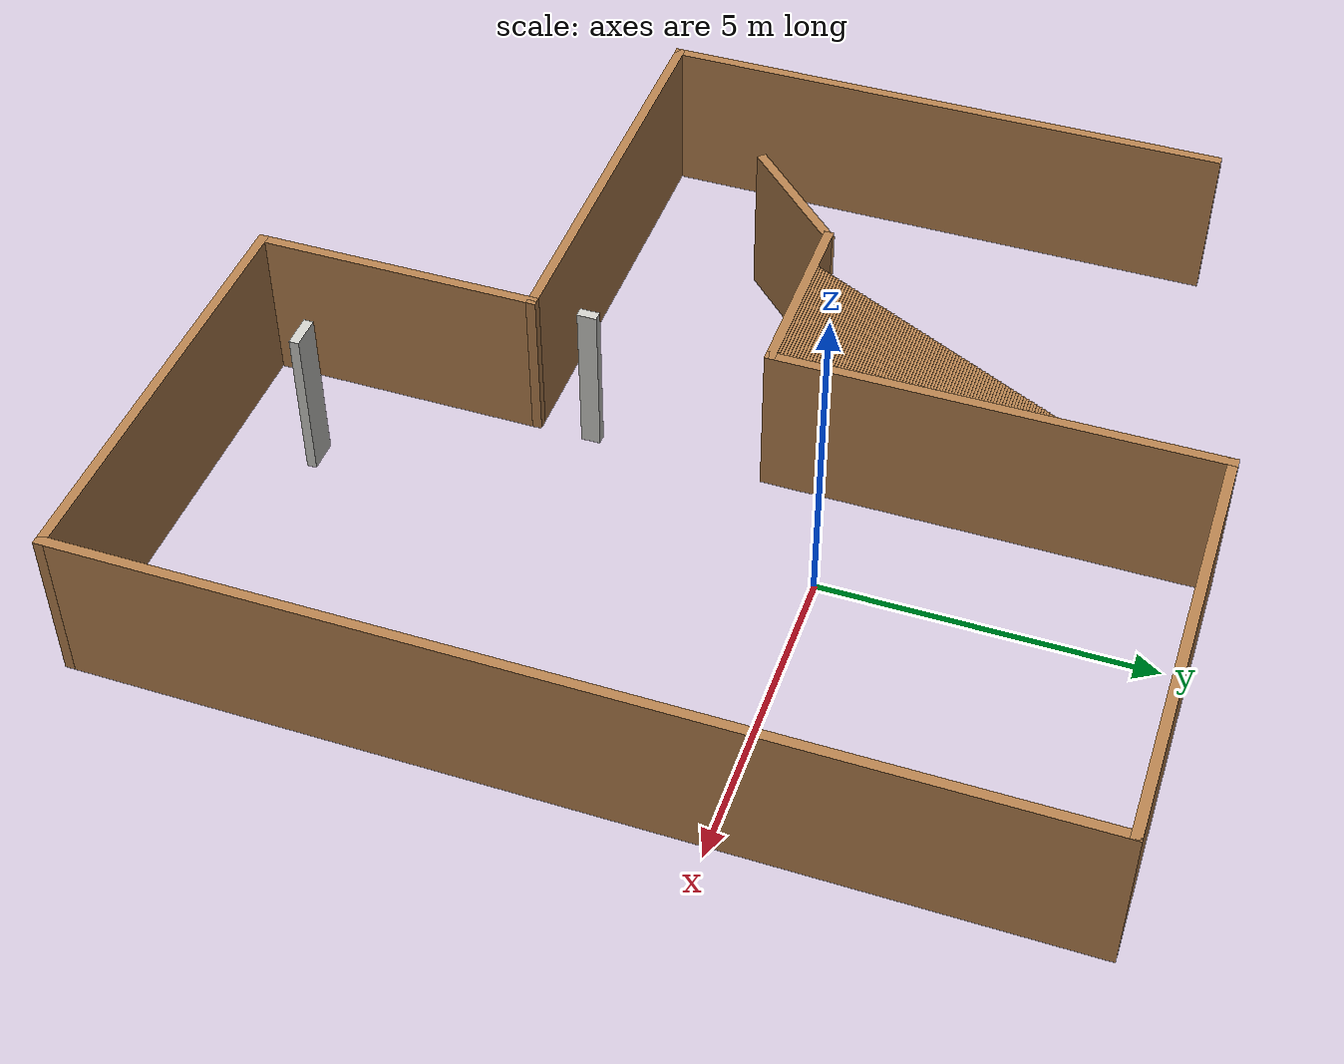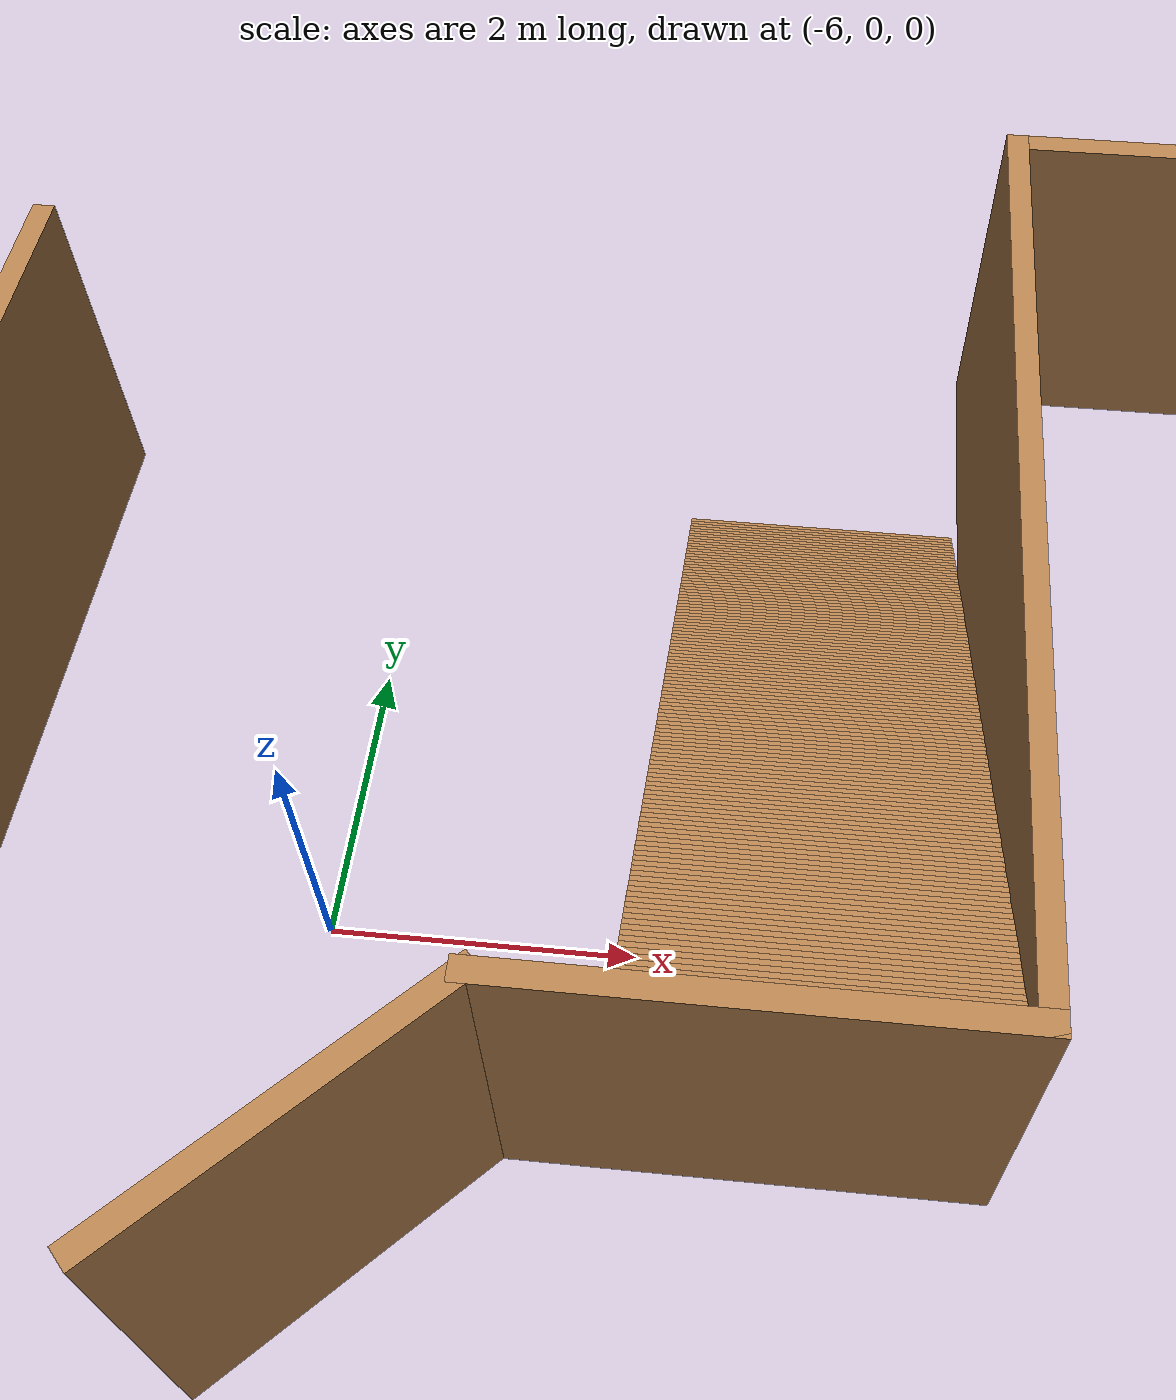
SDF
<?xml version='1.0'?>
<sdf version='1.7'>
  <model name='mundo_normal1'>
    <pose>-1.83298 -2.00796 0 0 -0 0</pose>
    <link name='Stairs_4'>
      <visual name='Stairs_4_Visual_0'>
        <pose>-1.12037 5.70373 0.010417 0 -0 0</pose>
        <geometry>
          <box>
            <size>2 0.041667 0.020833</size>
          </box>
        </geometry>
        <material>
          <script>
            <uri>file://media/materials/scripts/gazebo.material</uri>
            <name>Gazebo/Wood</name>
          </script>
          <ambient>1 1 1 1</ambient>
        </material>
        <meta>
          <layer>0</layer>
        </meta>
      </visual>
      <collision name='Stairs_4_Collision_0'>
        <geometry>
          <box>
            <size>2 0.041667 0.020833</size>
          </box>
        </geometry>
        <pose>-1.12037 5.70373 0.010417 0 -0 0</pose>
      </collision>
      <visual name='Stairs_4_Visual_1'>
        <pose>-1.12037 5.66206 0.03125 0 -0 0</pose>
        <geometry>
          <box>
            <size>2 0.041667 0.020833</size>
          </box>
        </geometry>
        <material>
          <script>
            <uri>file://media/materials/scripts/gazebo.material</uri>
            <name>Gazebo/Wood</name>
          </script>
          <ambient>1 1 1 1</ambient>
        </material>
        <meta>
          <layer>0</layer>
        </meta>
      </visual>
      <collision name='Stairs_4_Collision_1'>
        <geometry>
          <box>
            <size>2 0.041667 0.020833</size>
          </box>
        </geometry>
        <pose>-1.12037 5.66206 0.03125 0 -0 0</pose>
      </collision>
      <visual name='Stairs_4_Visual_2'>
        <pose>-1.12037 5.62039 0.052083 0 -0 0</pose>
        <geometry>
          <box>
            <size>2 0.041667 0.020833</size>
          </box>
        </geometry>
        <material>
          <script>
            <uri>file://media/materials/scripts/gazebo.material</uri>
            <name>Gazebo/Wood</name>
          </script>
          <ambient>1 1 1 1</ambient>
        </material>
        <meta>
          <layer>0</layer>
        </meta>
      </visual>
      <collision name='Stairs_4_Collision_2'>
        <geometry>
          <box>
            <size>2 0.041667 0.020833</size>
          </box>
        </geometry>
        <pose>-1.12037 5.62039 0.052083 0 -0 0</pose>
      </collision>
      <visual name='Stairs_4_Visual_3'>
        <pose>-1.12037 5.57873 0.072917 0 -0 0</pose>
        <geometry>
          <box>
            <size>2 0.041667 0.020833</size>
          </box>
        </geometry>
        <material>
          <script>
            <uri>file://media/materials/scripts/gazebo.material</uri>
            <name>Gazebo/Wood</name>
          </script>
          <ambient>1 1 1 1</ambient>
        </material>
        <meta>
          <layer>0</layer>
        </meta>
      </visual>
      <collision name='Stairs_4_Collision_3'>
        <geometry>
          <box>
            <size>2 0.041667 0.020833</size>
          </box>
        </geometry>
        <pose>-1.12037 5.57873 0.072917 0 -0 0</pose>
      </collision>
      <visual name='Stairs_4_Visual_4'>
        <pose>-1.12037 5.53706 0.09375 0 -0 0</pose>
        <geometry>
          <box>
            <size>2 0.041667 0.020833</size>
          </box>
        </geometry>
        <material>
          <script>
            <uri>file://media/materials/scripts/gazebo.material</uri>
            <name>Gazebo/Wood</name>
          </script>
          <ambient>1 1 1 1</ambient>
        </material>
        <meta>
          <layer>0</layer>
        </meta>
      </visual>
      <collision name='Stairs_4_Collision_4'>
        <geometry>
          <box>
            <size>2 0.041667 0.020833</size>
          </box>
        </geometry>
        <pose>-1.12037 5.53706 0.09375 0 -0 0</pose>
      </collision>
      <visual name='Stairs_4_Visual_5'>
        <pose>-1.12037 5.49539 0.114583 0 -0 0</pose>
        <geometry>
          <box>
            <size>2 0.041667 0.020833</size>
          </box>
        </geometry>
        <material>
          <script>
            <uri>file://media/materials/scripts/gazebo.material</uri>
            <name>Gazebo/Wood</name>
          </script>
          <ambient>1 1 1 1</ambient>
        </material>
        <meta>
          <layer>0</layer>
        </meta>
      </visual>
      <collision name='Stairs_4_Collision_5'>
        <geometry>
          <box>
            <size>2 0.041667 0.020833</size>
          </box>
        </geometry>
        <pose>-1.12037 5.49539 0.114583 0 -0 0</pose>
      </collision>
      <visual name='Stairs_4_Visual_6'>
        <pose>-1.12037 5.45372 0.135417 0 -0 0</pose>
        <geometry>
          <box>
            <size>2 0.041667 0.020833</size>
          </box>
        </geometry>
        <material>
          <script>
            <uri>file://media/materials/scripts/gazebo.material</uri>
            <name>Gazebo/Wood</name>
          </script>
          <ambient>1 1 1 1</ambient>
        </material>
        <meta>
          <layer>0</layer>
        </meta>
      </visual>
      <collision name='Stairs_4_Collision_6'>
        <geometry>
          <box>
            <size>2 0.041667 0.020833</size>
          </box>
        </geometry>
        <pose>-1.12037 5.45372 0.135417 0 -0 0</pose>
      </collision>
      <visual name='Stairs_4_Visual_7'>
        <pose>-1.12037 5.41206 0.15625 0 -0 0</pose>
        <geometry>
          <box>
            <size>2 0.041667 0.020833</size>
          </box>
        </geometry>
        <material>
          <script>
            <uri>file://media/materials/scripts/gazebo.material</uri>
            <name>Gazebo/Wood</name>
          </script>
          <ambient>1 1 1 1</ambient>
        </material>
        <meta>
          <layer>0</layer>
        </meta>
      </visual>
      <collision name='Stairs_4_Collision_7'>
        <geometry>
          <box>
            <size>2 0.041667 0.020833</size>
          </box>
        </geometry>
        <pose>-1.12037 5.41206 0.15625 0 -0 0</pose>
      </collision>
      <visual name='Stairs_4_Visual_8'>
        <pose>-1.12037 5.37039 0.177083 0 -0 0</pose>
        <geometry>
          <box>
            <size>2 0.041667 0.020833</size>
          </box>
        </geometry>
        <material>
          <script>
            <uri>file://media/materials/scripts/gazebo.material</uri>
            <name>Gazebo/Wood</name>
          </script>
          <ambient>1 1 1 1</ambient>
        </material>
        <meta>
          <layer>0</layer>
        </meta>
      </visual>
      <collision name='Stairs_4_Collision_8'>
        <geometry>
          <box>
            <size>2 0.041667 0.020833</size>
          </box>
        </geometry>
        <pose>-1.12037 5.37039 0.177083 0 -0 0</pose>
      </collision>
      <visual name='Stairs_4_Visual_9'>
        <pose>-1.12037 5.32872 0.197917 0 -0 0</pose>
        <geometry>
          <box>
            <size>2 0.041667 0.020833</size>
          </box>
        </geometry>
        <material>
          <script>
            <uri>file://media/materials/scripts/gazebo.material</uri>
            <name>Gazebo/Wood</name>
          </script>
          <ambient>1 1 1 1</ambient>
        </material>
        <meta>
          <layer>0</layer>
        </meta>
      </visual>
      <collision name='Stairs_4_Collision_9'>
        <geometry>
          <box>
            <size>2 0.041667 0.020833</size>
          </box>
        </geometry>
        <pose>-1.12037 5.32872 0.197917 0 -0 0</pose>
      </collision>
      <visual name='Stairs_4_Visual_10'>
        <pose>-1.12037 5.28706 0.21875 0 -0 0</pose>
        <geometry>
          <box>
            <size>2 0.041667 0.020833</size>
          </box>
        </geometry>
        <material>
          <script>
            <uri>file://media/materials/scripts/gazebo.material</uri>
            <name>Gazebo/Wood</name>
          </script>
          <ambient>1 1 1 1</ambient>
        </material>
        <meta>
          <layer>0</layer>
        </meta>
      </visual>
      <collision name='Stairs_4_Collision_10'>
        <geometry>
          <box>
            <size>2 0.041667 0.020833</size>
          </box>
        </geometry>
        <pose>-1.12037 5.28706 0.21875 0 -0 0</pose>
      </collision>
      <visual name='Stairs_4_Visual_11'>
        <pose>-1.12037 5.24539 0.239583 0 -0 0</pose>
        <geometry>
          <box>
            <size>2 0.041667 0.020833</size>
          </box>
        </geometry>
        <material>
          <script>
            <uri>file://media/materials/scripts/gazebo.material</uri>
            <name>Gazebo/Wood</name>
          </script>
          <ambient>1 1 1 1</ambient>
        </material>
        <meta>
          <layer>0</layer>
        </meta>
      </visual>
      <collision name='Stairs_4_Collision_11'>
        <geometry>
          <box>
            <size>2 0.041667 0.020833</size>
          </box>
        </geometry>
        <pose>-1.12037 5.24539 0.239583 0 -0 0</pose>
      </collision>
      <visual name='Stairs_4_Visual_12'>
        <pose>-1.12037 5.20373 0.260417 0 -0 0</pose>
        <geometry>
          <box>
            <size>2 0.041667 0.020833</size>
          </box>
        </geometry>
        <material>
          <script>
            <uri>file://media/materials/scripts/gazebo.material</uri>
            <name>Gazebo/Wood</name>
          </script>
          <ambient>1 1 1 1</ambient>
        </material>
        <meta>
          <layer>0</layer>
        </meta>
      </visual>
      <collision name='Stairs_4_Collision_12'>
        <geometry>
          <box>
            <size>2 0.041667 0.020833</size>
          </box>
        </geometry>
        <pose>-1.12037 5.20373 0.260417 0 -0 0</pose>
      </collision>
      <visual name='Stairs_4_Visual_13'>
        <pose>-1.12037 5.16206 0.28125 0 -0 0</pose>
        <geometry>
          <box>
            <size>2 0.041667 0.020833</size>
          </box>
        </geometry>
        <material>
          <script>
            <uri>file://media/materials/scripts/gazebo.material</uri>
            <name>Gazebo/Wood</name>
          </script>
          <ambient>1 1 1 1</ambient>
        </material>
        <meta>
          <layer>0</layer>
        </meta>
      </visual>
      <collision name='Stairs_4_Collision_13'>
        <geometry>
          <box>
            <size>2 0.041667 0.020833</size>
          </box>
        </geometry>
        <pose>-1.12037 5.16206 0.28125 0 -0 0</pose>
      </collision>
      <visual name='Stairs_4_Visual_14'>
        <pose>-1.12037 5.12039 0.302083 0 -0 0</pose>
        <geometry>
          <box>
            <size>2 0.041667 0.020833</size>
          </box>
        </geometry>
        <material>
          <script>
            <uri>file://media/materials/scripts/gazebo.material</uri>
            <name>Gazebo/Wood</name>
          </script>
          <ambient>1 1 1 1</ambient>
        </material>
        <meta>
          <layer>0</layer>
        </meta>
      </visual>
      <collision name='Stairs_4_Collision_14'>
        <geometry>
          <box>
            <size>2 0.041667 0.020833</size>
          </box>
        </geometry>
        <pose>-1.12037 5.12039 0.302083 0 -0 0</pose>
      </collision>
      <visual name='Stairs_4_Visual_15'>
        <pose>-1.12037 5.07873 0.322917 0 -0 0</pose>
        <geometry>
          <box>
            <size>2 0.041667 0.020833</size>
          </box>
        </geometry>
        <material>
          <script>
            <uri>file://media/materials/scripts/gazebo.material</uri>
            <name>Gazebo/Wood</name>
          </script>
          <ambient>1 1 1 1</ambient>
        </material>
        <meta>
          <layer>0</layer>
        </meta>
      </visual>
      <collision name='Stairs_4_Collision_15'>
        <geometry>
          <box>
            <size>2 0.041667 0.020833</size>
          </box>
        </geometry>
        <pose>-1.12037 5.07873 0.322917 0 -0 0</pose>
      </collision>
      <visual name='Stairs_4_Visual_16'>
        <pose>-1.12037 5.03706 0.34375 0 -0 0</pose>
        <geometry>
          <box>
            <size>2 0.041667 0.020833</size>
          </box>
        </geometry>
        <material>
          <script>
            <uri>file://media/materials/scripts/gazebo.material</uri>
            <name>Gazebo/Wood</name>
          </script>
          <ambient>1 1 1 1</ambient>
        </material>
        <meta>
          <layer>0</layer>
        </meta>
      </visual>
      <collision name='Stairs_4_Collision_16'>
        <geometry>
          <box>
            <size>2 0.041667 0.020833</size>
          </box>
        </geometry>
        <pose>-1.12037 5.03706 0.34375 0 -0 0</pose>
      </collision>
      <visual name='Stairs_4_Visual_17'>
        <pose>-1.12037 4.99539 0.364583 0 -0 0</pose>
        <geometry>
          <box>
            <size>2 0.041667 0.020833</size>
          </box>
        </geometry>
        <material>
          <script>
            <uri>file://media/materials/scripts/gazebo.material</uri>
            <name>Gazebo/Wood</name>
          </script>
          <ambient>1 1 1 1</ambient>
        </material>
        <meta>
          <layer>0</layer>
        </meta>
      </visual>
      <collision name='Stairs_4_Collision_17'>
        <geometry>
          <box>
            <size>2 0.041667 0.020833</size>
          </box>
        </geometry>
        <pose>-1.12037 4.99539 0.364583 0 -0 0</pose>
      </collision>
      <visual name='Stairs_4_Visual_18'>
        <pose>-1.12037 4.95372 0.385417 0 -0 0</pose>
        <geometry>
          <box>
            <size>2 0.041667 0.020833</size>
          </box>
        </geometry>
        <material>
          <script>
            <uri>file://media/materials/scripts/gazebo.material</uri>
            <name>Gazebo/Wood</name>
          </script>
          <ambient>1 1 1 1</ambient>
        </material>
        <meta>
          <layer>0</layer>
        </meta>
      </visual>
      <collision name='Stairs_4_Collision_18'>
        <geometry>
          <box>
            <size>2 0.041667 0.020833</size>
          </box>
        </geometry>
        <pose>-1.12037 4.95372 0.385417 0 -0 0</pose>
      </collision>
      <visual name='Stairs_4_Visual_19'>
        <pose>-1.12037 4.91206 0.40625 0 -0 0</pose>
        <geometry>
          <box>
            <size>2 0.041667 0.020833</size>
          </box>
        </geometry>
        <material>
          <script>
            <uri>file://media/materials/scripts/gazebo.material</uri>
            <name>Gazebo/Wood</name>
          </script>
          <ambient>1 1 1 1</ambient>
        </material>
        <meta>
          <layer>0</layer>
        </meta>
      </visual>
      <collision name='Stairs_4_Collision_19'>
        <geometry>
          <box>
            <size>2 0.041667 0.020833</size>
          </box>
        </geometry>
        <pose>-1.12037 4.91206 0.40625 0 -0 0</pose>
      </collision>
      <visual name='Stairs_4_Visual_20'>
        <pose>-1.12037 4.87039 0.427083 0 -0 0</pose>
        <geometry>
          <box>
            <size>2 0.041667 0.020833</size>
          </box>
        </geometry>
        <material>
          <script>
            <uri>file://media/materials/scripts/gazebo.material</uri>
            <name>Gazebo/Wood</name>
          </script>
          <ambient>1 1 1 1</ambient>
        </material>
        <meta>
          <layer>0</layer>
        </meta>
      </visual>
      <collision name='Stairs_4_Collision_20'>
        <geometry>
          <box>
            <size>2 0.041667 0.020833</size>
          </box>
        </geometry>
        <pose>-1.12037 4.87039 0.427083 0 -0 0</pose>
      </collision>
      <visual name='Stairs_4_Visual_21'>
        <pose>-1.12037 4.82872 0.447917 0 -0 0</pose>
        <geometry>
          <box>
            <size>2 0.041667 0.020833</size>
          </box>
        </geometry>
        <material>
          <script>
            <uri>file://media/materials/scripts/gazebo.material</uri>
            <name>Gazebo/Wood</name>
          </script>
          <ambient>1 1 1 1</ambient>
        </material>
        <meta>
          <layer>0</layer>
        </meta>
      </visual>
      <collision name='Stairs_4_Collision_21'>
        <geometry>
          <box>
            <size>2 0.041667 0.020833</size>
          </box>
        </geometry>
        <pose>-1.12037 4.82872 0.447917 0 -0 0</pose>
      </collision>
      <visual name='Stairs_4_Visual_22'>
        <pose>-1.12037 4.78706 0.46875 0 -0 0</pose>
        <geometry>
          <box>
            <size>2 0.041667 0.020833</size>
          </box>
        </geometry>
        <material>
          <script>
            <uri>file://media/materials/scripts/gazebo.material</uri>
            <name>Gazebo/Wood</name>
          </script>
          <ambient>1 1 1 1</ambient>
        </material>
        <meta>
          <layer>0</layer>
        </meta>
      </visual>
      <collision name='Stairs_4_Collision_22'>
        <geometry>
          <box>
            <size>2 0.041667 0.020833</size>
          </box>
        </geometry>
        <pose>-1.12037 4.78706 0.46875 0 -0 0</pose>
      </collision>
      <visual name='Stairs_4_Visual_23'>
        <pose>-1.12037 4.74539 0.489583 0 -0 0</pose>
        <geometry>
          <box>
            <size>2 0.041667 0.020833</size>
          </box>
        </geometry>
        <material>
          <script>
            <uri>file://media/materials/scripts/gazebo.material</uri>
            <name>Gazebo/Wood</name>
          </script>
          <ambient>1 1 1 1</ambient>
        </material>
        <meta>
          <layer>0</layer>
        </meta>
      </visual>
      <collision name='Stairs_4_Collision_23'>
        <geometry>
          <box>
            <size>2 0.041667 0.020833</size>
          </box>
        </geometry>
        <pose>-1.12037 4.74539 0.489583 0 -0 0</pose>
      </collision>
      <visual name='Stairs_4_Visual_24'>
        <pose>-1.12037 4.70372 0.510417 0 -0 0</pose>
        <geometry>
          <box>
            <size>2 0.041667 0.020833</size>
          </box>
        </geometry>
        <material>
          <script>
            <uri>file://media/materials/scripts/gazebo.material</uri>
            <name>Gazebo/Wood</name>
          </script>
          <ambient>1 1 1 1</ambient>
        </material>
        <meta>
          <layer>0</layer>
        </meta>
      </visual>
      <collision name='Stairs_4_Collision_24'>
        <geometry>
          <box>
            <size>2 0.041667 0.020833</size>
          </box>
        </geometry>
        <pose>-1.12037 4.70372 0.510417 0 -0 0</pose>
      </collision>
      <visual name='Stairs_4_Visual_25'>
        <pose>-1.12037 4.66206 0.53125 0 -0 0</pose>
        <geometry>
          <box>
            <size>2 0.041667 0.020833</size>
          </box>
        </geometry>
        <material>
          <script>
            <uri>file://media/materials/scripts/gazebo.material</uri>
            <name>Gazebo/Wood</name>
          </script>
          <ambient>1 1 1 1</ambient>
        </material>
        <meta>
          <layer>0</layer>
        </meta>
      </visual>
      <collision name='Stairs_4_Collision_25'>
        <geometry>
          <box>
            <size>2 0.041667 0.020833</size>
          </box>
        </geometry>
        <pose>-1.12037 4.66206 0.53125 0 -0 0</pose>
      </collision>
      <visual name='Stairs_4_Visual_26'>
        <pose>-1.12037 4.62039 0.552083 0 -0 0</pose>
        <geometry>
          <box>
            <size>2 0.041667 0.020833</size>
          </box>
        </geometry>
        <material>
          <script>
            <uri>file://media/materials/scripts/gazebo.material</uri>
            <name>Gazebo/Wood</name>
          </script>
          <ambient>1 1 1 1</ambient>
        </material>
        <meta>
          <layer>0</layer>
        </meta>
      </visual>
      <collision name='Stairs_4_Collision_26'>
        <geometry>
          <box>
            <size>2 0.041667 0.020833</size>
          </box>
        </geometry>
        <pose>-1.12037 4.62039 0.552083 0 -0 0</pose>
      </collision>
      <visual name='Stairs_4_Visual_27'>
        <pose>-1.12037 4.57873 0.572917 0 -0 0</pose>
        <geometry>
          <box>
            <size>2 0.041667 0.020833</size>
          </box>
        </geometry>
        <material>
          <script>
            <uri>file://media/materials/scripts/gazebo.material</uri>
            <name>Gazebo/Wood</name>
          </script>
          <ambient>1 1 1 1</ambient>
        </material>
        <meta>
          <layer>0</layer>
        </meta>
      </visual>
      <collision name='Stairs_4_Collision_27'>
        <geometry>
          <box>
            <size>2 0.041667 0.020833</size>
          </box>
        </geometry>
        <pose>-1.12037 4.57873 0.572917 0 -0 0</pose>
      </collision>
      <visual name='Stairs_4_Visual_28'>
        <pose>-1.12037 4.53706 0.59375 0 -0 0</pose>
        <geometry>
          <box>
            <size>2 0.041667 0.020833</size>
          </box>
        </geometry>
        <material>
          <script>
            <uri>file://media/materials/scripts/gazebo.material</uri>
            <name>Gazebo/Wood</name>
          </script>
          <ambient>1 1 1 1</ambient>
        </material>
        <meta>
          <layer>0</layer>
        </meta>
      </visual>
      <collision name='Stairs_4_Collision_28'>
        <geometry>
          <box>
            <size>2 0.041667 0.020833</size>
          </box>
        </geometry>
        <pose>-1.12037 4.53706 0.59375 0 -0 0</pose>
      </collision>
      <visual name='Stairs_4_Visual_29'>
        <pose>-1.12037 4.49539 0.614583 0 -0 0</pose>
        <geometry>
          <box>
            <size>2 0.041667 0.020833</size>
          </box>
        </geometry>
        <material>
          <script>
            <uri>file://media/materials/scripts/gazebo.material</uri>
            <name>Gazebo/Wood</name>
          </script>
          <ambient>1 1 1 1</ambient>
        </material>
        <meta>
          <layer>0</layer>
        </meta>
      </visual>
      <collision name='Stairs_4_Collision_29'>
        <geometry>
          <box>
            <size>2 0.041667 0.020833</size>
          </box>
        </geometry>
        <pose>-1.12037 4.49539 0.614583 0 -0 0</pose>
      </collision>
      <visual name='Stairs_4_Visual_30'>
        <pose>-1.12037 4.45373 0.635417 0 -0 0</pose>
        <geometry>
          <box>
            <size>2 0.041667 0.020833</size>
          </box>
        </geometry>
        <material>
          <script>
            <uri>file://media/materials/scripts/gazebo.material</uri>
            <name>Gazebo/Wood</name>
          </script>
          <ambient>1 1 1 1</ambient>
        </material>
        <meta>
          <layer>0</layer>
        </meta>
      </visual>
      <collision name='Stairs_4_Collision_30'>
        <geometry>
          <box>
            <size>2 0.041667 0.020833</size>
          </box>
        </geometry>
        <pose>-1.12037 4.45373 0.635417 0 -0 0</pose>
      </collision>
      <visual name='Stairs_4_Visual_31'>
        <pose>-1.12037 4.41206 0.65625 0 -0 0</pose>
        <geometry>
          <box>
            <size>2 0.041667 0.020833</size>
          </box>
        </geometry>
        <material>
          <script>
            <uri>file://media/materials/scripts/gazebo.material</uri>
            <name>Gazebo/Wood</name>
          </script>
          <ambient>1 1 1 1</ambient>
        </material>
        <meta>
          <layer>0</layer>
        </meta>
      </visual>
      <collision name='Stairs_4_Collision_31'>
        <geometry>
          <box>
            <size>2 0.041667 0.020833</size>
          </box>
        </geometry>
        <pose>-1.12037 4.41206 0.65625 0 -0 0</pose>
      </collision>
      <visual name='Stairs_4_Visual_32'>
        <pose>-1.12037 4.37039 0.677083 0 -0 0</pose>
        <geometry>
          <box>
            <size>2 0.041667 0.020833</size>
          </box>
        </geometry>
        <material>
          <script>
            <uri>file://media/materials/scripts/gazebo.material</uri>
            <name>Gazebo/Wood</name>
          </script>
          <ambient>1 1 1 1</ambient>
        </material>
        <meta>
          <layer>0</layer>
        </meta>
      </visual>
      <collision name='Stairs_4_Collision_32'>
        <geometry>
          <box>
            <size>2 0.041667 0.020833</size>
          </box>
        </geometry>
        <pose>-1.12037 4.37039 0.677083 0 -0 0</pose>
      </collision>
      <visual name='Stairs_4_Visual_33'>
        <pose>-1.12037 4.32872 0.697917 0 -0 0</pose>
        <geometry>
          <box>
            <size>2 0.041667 0.020833</size>
          </box>
        </geometry>
        <material>
          <script>
            <uri>file://media/materials/scripts/gazebo.material</uri>
            <name>Gazebo/Wood</name>
          </script>
          <ambient>1 1 1 1</ambient>
        </material>
        <meta>
          <layer>0</layer>
        </meta>
      </visual>
      <collision name='Stairs_4_Collision_33'>
        <geometry>
          <box>
            <size>2 0.041667 0.020833</size>
          </box>
        </geometry>
        <pose>-1.12037 4.32872 0.697917 0 -0 0</pose>
      </collision>
      <visual name='Stairs_4_Visual_34'>
        <pose>-1.12037 4.28706 0.71875 0 -0 0</pose>
        <geometry>
          <box>
            <size>2 0.041667 0.020833</size>
          </box>
        </geometry>
        <material>
          <script>
            <uri>file://media/materials/scripts/gazebo.material</uri>
            <name>Gazebo/Wood</name>
          </script>
          <ambient>1 1 1 1</ambient>
        </material>
        <meta>
          <layer>0</layer>
        </meta>
      </visual>
      <collision name='Stairs_4_Collision_34'>
        <geometry>
          <box>
            <size>2 0.041667 0.020833</size>
          </box>
        </geometry>
        <pose>-1.12037 4.28706 0.71875 0 -0 0</pose>
      </collision>
      <visual name='Stairs_4_Visual_35'>
        <pose>-1.12037 4.24539 0.739583 0 -0 0</pose>
        <geometry>
          <box>
            <size>2 0.041667 0.020833</size>
          </box>
        </geometry>
        <material>
          <script>
            <uri>file://media/materials/scripts/gazebo.material</uri>
            <name>Gazebo/Wood</name>
          </script>
          <ambient>1 1 1 1</ambient>
        </material>
        <meta>
          <layer>0</layer>
        </meta>
      </visual>
      <collision name='Stairs_4_Collision_35'>
        <geometry>
          <box>
            <size>2 0.041667 0.020833</size>
          </box>
        </geometry>
        <pose>-1.12037 4.24539 0.739583 0 -0 0</pose>
      </collision>
      <visual name='Stairs_4_Visual_36'>
        <pose>-1.12037 4.20373 0.760417 0 -0 0</pose>
        <geometry>
          <box>
            <size>2 0.041667 0.020833</size>
          </box>
        </geometry>
        <material>
          <script>
            <uri>file://media/materials/scripts/gazebo.material</uri>
            <name>Gazebo/Wood</name>
          </script>
          <ambient>1 1 1 1</ambient>
        </material>
        <meta>
          <layer>0</layer>
        </meta>
      </visual>
      <collision name='Stairs_4_Collision_36'>
        <geometry>
          <box>
            <size>2 0.041667 0.020833</size>
          </box>
        </geometry>
        <pose>-1.12037 4.20373 0.760417 0 -0 0</pose>
      </collision>
      <visual name='Stairs_4_Visual_37'>
        <pose>-1.12037 4.16206 0.78125 0 -0 0</pose>
        <geometry>
          <box>
            <size>2 0.041667 0.020833</size>
          </box>
        </geometry>
        <material>
          <script>
            <uri>file://media/materials/scripts/gazebo.material</uri>
            <name>Gazebo/Wood</name>
          </script>
          <ambient>1 1 1 1</ambient>
        </material>
        <meta>
          <layer>0</layer>
        </meta>
      </visual>
      <collision name='Stairs_4_Collision_37'>
        <geometry>
          <box>
            <size>2 0.041667 0.020833</size>
          </box>
        </geometry>
        <pose>-1.12037 4.16206 0.78125 0 -0 0</pose>
      </collision>
      <visual name='Stairs_4_Visual_38'>
        <pose>-1.12037 4.12039 0.802083 0 -0 0</pose>
        <geometry>
          <box>
            <size>2 0.041667 0.020833</size>
          </box>
        </geometry>
        <material>
          <script>
            <uri>file://media/materials/scripts/gazebo.material</uri>
            <name>Gazebo/Wood</name>
          </script>
          <ambient>1 1 1 1</ambient>
        </material>
        <meta>
          <layer>0</layer>
        </meta>
      </visual>
      <collision name='Stairs_4_Collision_38'>
        <geometry>
          <box>
            <size>2 0.041667 0.020833</size>
          </box>
        </geometry>
        <pose>-1.12037 4.12039 0.802083 0 -0 0</pose>
      </collision>
      <visual name='Stairs_4_Visual_39'>
        <pose>-1.12037 4.07873 0.822917 0 -0 0</pose>
        <geometry>
          <box>
            <size>2 0.041667 0.020833</size>
          </box>
        </geometry>
        <material>
          <script>
            <uri>file://media/materials/scripts/gazebo.material</uri>
            <name>Gazebo/Wood</name>
          </script>
          <ambient>1 1 1 1</ambient>
        </material>
        <meta>
          <layer>0</layer>
        </meta>
      </visual>
      <collision name='Stairs_4_Collision_39'>
        <geometry>
          <box>
            <size>2 0.041667 0.020833</size>
          </box>
        </geometry>
        <pose>-1.12037 4.07873 0.822917 0 -0 0</pose>
      </collision>
      <visual name='Stairs_4_Visual_40'>
        <pose>-1.12037 4.03706 0.84375 0 -0 0</pose>
        <geometry>
          <box>
            <size>2 0.041667 0.020833</size>
          </box>
        </geometry>
        <material>
          <script>
            <uri>file://media/materials/scripts/gazebo.material</uri>
            <name>Gazebo/Wood</name>
          </script>
          <ambient>1 1 1 1</ambient>
        </material>
        <meta>
          <layer>0</layer>
        </meta>
      </visual>
      <collision name='Stairs_4_Collision_40'>
        <geometry>
          <box>
            <size>2 0.041667 0.020833</size>
          </box>
        </geometry>
        <pose>-1.12037 4.03706 0.84375 0 -0 0</pose>
      </collision>
      <visual name='Stairs_4_Visual_41'>
        <pose>-1.12037 3.99539 0.864583 0 -0 0</pose>
        <geometry>
          <box>
            <size>2 0.041667 0.020833</size>
          </box>
        </geometry>
        <material>
          <script>
            <uri>file://media/materials/scripts/gazebo.material</uri>
            <name>Gazebo/Wood</name>
          </script>
          <ambient>1 1 1 1</ambient>
        </material>
        <meta>
          <layer>0</layer>
        </meta>
      </visual>
      <collision name='Stairs_4_Collision_41'>
        <geometry>
          <box>
            <size>2 0.041667 0.020833</size>
          </box>
        </geometry>
        <pose>-1.12037 3.99539 0.864583 0 -0 0</pose>
      </collision>
      <visual name='Stairs_4_Visual_42'>
        <pose>-1.12037 3.95372 0.885417 0 -0 0</pose>
        <geometry>
          <box>
            <size>2 0.041667 0.020833</size>
          </box>
        </geometry>
        <material>
          <script>
            <uri>file://media/materials/scripts/gazebo.material</uri>
            <name>Gazebo/Wood</name>
          </script>
          <ambient>1 1 1 1</ambient>
        </material>
        <meta>
          <layer>0</layer>
        </meta>
      </visual>
      <collision name='Stairs_4_Collision_42'>
        <geometry>
          <box>
            <size>2 0.041667 0.020833</size>
          </box>
        </geometry>
        <pose>-1.12037 3.95372 0.885417 0 -0 0</pose>
      </collision>
      <visual name='Stairs_4_Visual_43'>
        <pose>-1.12037 3.91206 0.90625 0 -0 0</pose>
        <geometry>
          <box>
            <size>2 0.041667 0.020833</size>
          </box>
        </geometry>
        <material>
          <script>
            <uri>file://media/materials/scripts/gazebo.material</uri>
            <name>Gazebo/Wood</name>
          </script>
          <ambient>1 1 1 1</ambient>
        </material>
        <meta>
          <layer>0</layer>
        </meta>
      </visual>
      <collision name='Stairs_4_Collision_43'>
        <geometry>
          <box>
            <size>2 0.041667 0.020833</size>
          </box>
        </geometry>
        <pose>-1.12037 3.91206 0.90625 0 -0 0</pose>
      </collision>
      <visual name='Stairs_4_Visual_44'>
        <pose>-1.12037 3.87039 0.927083 0 -0 0</pose>
        <geometry>
          <box>
            <size>2 0.041667 0.020833</size>
          </box>
        </geometry>
        <material>
          <script>
            <uri>file://media/materials/scripts/gazebo.material</uri>
            <name>Gazebo/Wood</name>
          </script>
          <ambient>1 1 1 1</ambient>
        </material>
        <meta>
          <layer>0</layer>
        </meta>
      </visual>
      <collision name='Stairs_4_Collision_44'>
        <geometry>
          <box>
            <size>2 0.041667 0.020833</size>
          </box>
        </geometry>
        <pose>-1.12037 3.87039 0.927083 0 -0 0</pose>
      </collision>
      <visual name='Stairs_4_Visual_45'>
        <pose>-1.12037 3.82872 0.947917 0 -0 0</pose>
        <geometry>
          <box>
            <size>2 0.041667 0.020833</size>
          </box>
        </geometry>
        <material>
          <script>
            <uri>file://media/materials/scripts/gazebo.material</uri>
            <name>Gazebo/Wood</name>
          </script>
          <ambient>1 1 1 1</ambient>
        </material>
        <meta>
          <layer>0</layer>
        </meta>
      </visual>
      <collision name='Stairs_4_Collision_45'>
        <geometry>
          <box>
            <size>2 0.041667 0.020833</size>
          </box>
        </geometry>
        <pose>-1.12037 3.82872 0.947917 0 -0 0</pose>
      </collision>
      <visual name='Stairs_4_Visual_46'>
        <pose>-1.12037 3.78706 0.96875 0 -0 0</pose>
        <geometry>
          <box>
            <size>2 0.041667 0.020833</size>
          </box>
        </geometry>
        <material>
          <script>
            <uri>file://media/materials/scripts/gazebo.material</uri>
            <name>Gazebo/Wood</name>
          </script>
          <ambient>1 1 1 1</ambient>
        </material>
        <meta>
          <layer>0</layer>
        </meta>
      </visual>
      <collision name='Stairs_4_Collision_46'>
        <geometry>
          <box>
            <size>2 0.041667 0.020833</size>
          </box>
        </geometry>
        <pose>-1.12037 3.78706 0.96875 0 -0 0</pose>
      </collision>
      <visual name='Stairs_4_Visual_47'>
        <pose>-1.12037 3.74539 0.989583 0 -0 0</pose>
        <geometry>
          <box>
            <size>2 0.041667 0.020833</size>
          </box>
        </geometry>
        <material>
          <script>
            <uri>file://media/materials/scripts/gazebo.material</uri>
            <name>Gazebo/Wood</name>
          </script>
          <ambient>1 1 1 1</ambient>
        </material>
        <meta>
          <layer>0</layer>
        </meta>
      </visual>
      <collision name='Stairs_4_Collision_47'>
        <geometry>
          <box>
            <size>2 0.041667 0.020833</size>
          </box>
        </geometry>
        <pose>-1.12037 3.74539 0.989583 0 -0 0</pose>
      </collision>
      <visual name='Stairs_4_Visual_48'>
        <pose>-1.12037 3.70372 1.01042 0 -0 0</pose>
        <geometry>
          <box>
            <size>2 0.041667 0.020833</size>
          </box>
        </geometry>
        <material>
          <script>
            <uri>file://media/materials/scripts/gazebo.material</uri>
            <name>Gazebo/Wood</name>
          </script>
          <ambient>1 1 1 1</ambient>
        </material>
        <meta>
          <layer>0</layer>
        </meta>
      </visual>
      <collision name='Stairs_4_Collision_48'>
        <geometry>
          <box>
            <size>2 0.041667 0.020833</size>
          </box>
        </geometry>
        <pose>-1.12037 3.70372 1.01042 0 -0 0</pose>
      </collision>
      <visual name='Stairs_4_Visual_49'>
        <pose>-1.12037 3.66206 1.03125 0 -0 0</pose>
        <geometry>
          <box>
            <size>2 0.041667 0.020833</size>
          </box>
        </geometry>
        <material>
          <script>
            <uri>file://media/materials/scripts/gazebo.material</uri>
            <name>Gazebo/Wood</name>
          </script>
          <ambient>1 1 1 1</ambient>
        </material>
        <meta>
          <layer>0</layer>
        </meta>
      </visual>
      <collision name='Stairs_4_Collision_49'>
        <geometry>
          <box>
            <size>2 0.041667 0.020833</size>
          </box>
        </geometry>
        <pose>-1.12037 3.66206 1.03125 0 -0 0</pose>
      </collision>
      <visual name='Stairs_4_Visual_50'>
        <pose>-1.12037 3.62039 1.05208 0 -0 0</pose>
        <geometry>
          <box>
            <size>2 0.041667 0.020833</size>
          </box>
        </geometry>
        <material>
          <script>
            <uri>file://media/materials/scripts/gazebo.material</uri>
            <name>Gazebo/Wood</name>
          </script>
          <ambient>1 1 1 1</ambient>
        </material>
        <meta>
          <layer>0</layer>
        </meta>
      </visual>
      <collision name='Stairs_4_Collision_50'>
        <geometry>
          <box>
            <size>2 0.041667 0.020833</size>
          </box>
        </geometry>
        <pose>-1.12037 3.62039 1.05208 0 -0 0</pose>
      </collision>
      <visual name='Stairs_4_Visual_51'>
        <pose>-1.12037 3.57872 1.07292 0 -0 0</pose>
        <geometry>
          <box>
            <size>2 0.041667 0.020833</size>
          </box>
        </geometry>
        <material>
          <script>
            <uri>file://media/materials/scripts/gazebo.material</uri>
            <name>Gazebo/Wood</name>
          </script>
          <ambient>1 1 1 1</ambient>
        </material>
        <meta>
          <layer>0</layer>
        </meta>
      </visual>
      <collision name='Stairs_4_Collision_51'>
        <geometry>
          <box>
            <size>2 0.041667 0.020833</size>
          </box>
        </geometry>
        <pose>-1.12037 3.57872 1.07292 0 -0 0</pose>
      </collision>
      <visual name='Stairs_4_Visual_52'>
        <pose>-1.12037 3.53706 1.09375 0 -0 0</pose>
        <geometry>
          <box>
            <size>2 0.041667 0.020833</size>
          </box>
        </geometry>
        <material>
          <script>
            <uri>file://media/materials/scripts/gazebo.material</uri>
            <name>Gazebo/Wood</name>
          </script>
          <ambient>1 1 1 1</ambient>
        </material>
        <meta>
          <layer>0</layer>
        </meta>
      </visual>
      <collision name='Stairs_4_Collision_52'>
        <geometry>
          <box>
            <size>2 0.041667 0.020833</size>
          </box>
        </geometry>
        <pose>-1.12037 3.53706 1.09375 0 -0 0</pose>
      </collision>
      <visual name='Stairs_4_Visual_53'>
        <pose>-1.12037 3.49539 1.11458 0 -0 0</pose>
        <geometry>
          <box>
            <size>2 0.041667 0.020833</size>
          </box>
        </geometry>
        <material>
          <script>
            <uri>file://media/materials/scripts/gazebo.material</uri>
            <name>Gazebo/Wood</name>
          </script>
          <ambient>1 1 1 1</ambient>
        </material>
        <meta>
          <layer>0</layer>
        </meta>
      </visual>
      <collision name='Stairs_4_Collision_53'>
        <geometry>
          <box>
            <size>2 0.041667 0.020833</size>
          </box>
        </geometry>
        <pose>-1.12037 3.49539 1.11458 0 -0 0</pose>
      </collision>
      <visual name='Stairs_4_Visual_54'>
        <pose>-1.12037 3.45372 1.13542 0 -0 0</pose>
        <geometry>
          <box>
            <size>2 0.041667 0.020833</size>
          </box>
        </geometry>
        <material>
          <script>
            <uri>file://media/materials/scripts/gazebo.material</uri>
            <name>Gazebo/Wood</name>
          </script>
          <ambient>1 1 1 1</ambient>
        </material>
        <meta>
          <layer>0</layer>
        </meta>
      </visual>
      <collision name='Stairs_4_Collision_54'>
        <geometry>
          <box>
            <size>2 0.041667 0.020833</size>
          </box>
        </geometry>
        <pose>-1.12037 3.45372 1.13542 0 -0 0</pose>
      </collision>
      <visual name='Stairs_4_Visual_55'>
        <pose>-1.12037 3.41206 1.15625 0 -0 0</pose>
        <geometry>
          <box>
            <size>2 0.041667 0.020833</size>
          </box>
        </geometry>
        <material>
          <script>
            <uri>file://media/materials/scripts/gazebo.material</uri>
            <name>Gazebo/Wood</name>
          </script>
          <ambient>1 1 1 1</ambient>
        </material>
        <meta>
          <layer>0</layer>
        </meta>
      </visual>
      <collision name='Stairs_4_Collision_55'>
        <geometry>
          <box>
            <size>2 0.041667 0.020833</size>
          </box>
        </geometry>
        <pose>-1.12037 3.41206 1.15625 0 -0 0</pose>
      </collision>
      <visual name='Stairs_4_Visual_56'>
        <pose>-1.12037 3.37039 1.17708 0 -0 0</pose>
        <geometry>
          <box>
            <size>2 0.041667 0.020833</size>
          </box>
        </geometry>
        <material>
          <script>
            <uri>file://media/materials/scripts/gazebo.material</uri>
            <name>Gazebo/Wood</name>
          </script>
          <ambient>1 1 1 1</ambient>
        </material>
        <meta>
          <layer>0</layer>
        </meta>
      </visual>
      <collision name='Stairs_4_Collision_56'>
        <geometry>
          <box>
            <size>2 0.041667 0.020833</size>
          </box>
        </geometry>
        <pose>-1.12037 3.37039 1.17708 0 -0 0</pose>
      </collision>
      <visual name='Stairs_4_Visual_57'>
        <pose>-1.12037 3.32872 1.19792 0 -0 0</pose>
        <geometry>
          <box>
            <size>2 0.041667 0.020833</size>
          </box>
        </geometry>
        <material>
          <script>
            <uri>file://media/materials/scripts/gazebo.material</uri>
            <name>Gazebo/Wood</name>
          </script>
          <ambient>1 1 1 1</ambient>
        </material>
        <meta>
          <layer>0</layer>
        </meta>
      </visual>
      <collision name='Stairs_4_Collision_57'>
        <geometry>
          <box>
            <size>2 0.041667 0.020833</size>
          </box>
        </geometry>
        <pose>-1.12037 3.32872 1.19792 0 -0 0</pose>
      </collision>
      <visual name='Stairs_4_Visual_58'>
        <pose>-1.12037 3.28706 1.21875 0 -0 0</pose>
        <geometry>
          <box>
            <size>2 0.041667 0.020833</size>
          </box>
        </geometry>
        <material>
          <script>
            <uri>file://media/materials/scripts/gazebo.material</uri>
            <name>Gazebo/Wood</name>
          </script>
          <ambient>1 1 1 1</ambient>
        </material>
        <meta>
          <layer>0</layer>
        </meta>
      </visual>
      <collision name='Stairs_4_Collision_58'>
        <geometry>
          <box>
            <size>2 0.041667 0.020833</size>
          </box>
        </geometry>
        <pose>-1.12037 3.28706 1.21875 0 -0 0</pose>
      </collision>
      <visual name='Stairs_4_Visual_59'>
        <pose>-1.12037 3.24539 1.23958 0 -0 0</pose>
        <geometry>
          <box>
            <size>2 0.041667 0.020833</size>
          </box>
        </geometry>
        <material>
          <script>
            <uri>file://media/materials/scripts/gazebo.material</uri>
            <name>Gazebo/Wood</name>
          </script>
          <ambient>1 1 1 1</ambient>
        </material>
        <meta>
          <layer>0</layer>
        </meta>
      </visual>
      <collision name='Stairs_4_Collision_59'>
        <geometry>
          <box>
            <size>2 0.041667 0.020833</size>
          </box>
        </geometry>
        <pose>-1.12037 3.24539 1.23958 0 -0 0</pose>
      </collision>
      <visual name='Stairs_4_Visual_60'>
        <pose>-1.12037 3.20372 1.26042 0 -0 0</pose>
        <geometry>
          <box>
            <size>2 0.041667 0.020833</size>
          </box>
        </geometry>
        <material>
          <script>
            <uri>file://media/materials/scripts/gazebo.material</uri>
            <name>Gazebo/Wood</name>
          </script>
          <ambient>1 1 1 1</ambient>
        </material>
        <meta>
          <layer>0</layer>
        </meta>
      </visual>
      <collision name='Stairs_4_Collision_60'>
        <geometry>
          <box>
            <size>2 0.041667 0.020833</size>
          </box>
        </geometry>
        <pose>-1.12037 3.20372 1.26042 0 -0 0</pose>
      </collision>
      <visual name='Stairs_4_Visual_61'>
        <pose>-1.12037 3.16206 1.28125 0 -0 0</pose>
        <geometry>
          <box>
            <size>2 0.041667 0.020833</size>
          </box>
        </geometry>
        <material>
          <script>
            <uri>file://media/materials/scripts/gazebo.material</uri>
            <name>Gazebo/Wood</name>
          </script>
          <ambient>1 1 1 1</ambient>
        </material>
        <meta>
          <layer>0</layer>
        </meta>
      </visual>
      <collision name='Stairs_4_Collision_61'>
        <geometry>
          <box>
            <size>2 0.041667 0.020833</size>
          </box>
        </geometry>
        <pose>-1.12037 3.16206 1.28125 0 -0 0</pose>
      </collision>
      <visual name='Stairs_4_Visual_62'>
        <pose>-1.12037 3.12039 1.30208 0 -0 0</pose>
        <geometry>
          <box>
            <size>2 0.041667 0.020833</size>
          </box>
        </geometry>
        <material>
          <script>
            <uri>file://media/materials/scripts/gazebo.material</uri>
            <name>Gazebo/Wood</name>
          </script>
          <ambient>1 1 1 1</ambient>
        </material>
        <meta>
          <layer>0</layer>
        </meta>
      </visual>
      <collision name='Stairs_4_Collision_62'>
        <geometry>
          <box>
            <size>2 0.041667 0.020833</size>
          </box>
        </geometry>
        <pose>-1.12037 3.12039 1.30208 0 -0 0</pose>
      </collision>
      <visual name='Stairs_4_Visual_63'>
        <pose>-1.12037 3.07872 1.32292 0 -0 0</pose>
        <geometry>
          <box>
            <size>2 0.041667 0.020833</size>
          </box>
        </geometry>
        <material>
          <script>
            <uri>file://media/materials/scripts/gazebo.material</uri>
            <name>Gazebo/Wood</name>
          </script>
          <ambient>1 1 1 1</ambient>
        </material>
        <meta>
          <layer>0</layer>
        </meta>
      </visual>
      <collision name='Stairs_4_Collision_63'>
        <geometry>
          <box>
            <size>2 0.041667 0.020833</size>
          </box>
        </geometry>
        <pose>-1.12037 3.07872 1.32292 0 -0 0</pose>
      </collision>
      <visual name='Stairs_4_Visual_64'>
        <pose>-1.12037 3.03706 1.34375 0 -0 0</pose>
        <geometry>
          <box>
            <size>2 0.041667 0.020833</size>
          </box>
        </geometry>
        <material>
          <script>
            <uri>file://media/materials/scripts/gazebo.material</uri>
            <name>Gazebo/Wood</name>
          </script>
          <ambient>1 1 1 1</ambient>
        </material>
        <meta>
          <layer>0</layer>
        </meta>
      </visual>
      <collision name='Stairs_4_Collision_64'>
        <geometry>
          <box>
            <size>2 0.041667 0.020833</size>
          </box>
        </geometry>
        <pose>-1.12037 3.03706 1.34375 0 -0 0</pose>
      </collision>
      <visual name='Stairs_4_Visual_65'>
        <pose>-1.12037 2.99539 1.36458 0 -0 0</pose>
        <geometry>
          <box>
            <size>2 0.041667 0.020833</size>
          </box>
        </geometry>
        <material>
          <script>
            <uri>file://media/materials/scripts/gazebo.material</uri>
            <name>Gazebo/Wood</name>
          </script>
          <ambient>1 1 1 1</ambient>
        </material>
        <meta>
          <layer>0</layer>
        </meta>
      </visual>
      <collision name='Stairs_4_Collision_65'>
        <geometry>
          <box>
            <size>2 0.041667 0.020833</size>
          </box>
        </geometry>
        <pose>-1.12037 2.99539 1.36458 0 -0 0</pose>
      </collision>
      <visual name='Stairs_4_Visual_66'>
        <pose>-1.12037 2.95372 1.38542 0 -0 0</pose>
        <geometry>
          <box>
            <size>2 0.041667 0.020833</size>
          </box>
        </geometry>
        <material>
          <script>
            <uri>file://media/materials/scripts/gazebo.material</uri>
            <name>Gazebo/Wood</name>
          </script>
          <ambient>1 1 1 1</ambient>
        </material>
        <meta>
          <layer>0</layer>
        </meta>
      </visual>
      <collision name='Stairs_4_Collision_66'>
        <geometry>
          <box>
            <size>2 0.041667 0.020833</size>
          </box>
        </geometry>
        <pose>-1.12037 2.95372 1.38542 0 -0 0</pose>
      </collision>
      <visual name='Stairs_4_Visual_67'>
        <pose>-1.12037 2.91206 1.40625 0 -0 0</pose>
        <geometry>
          <box>
            <size>2 0.041667 0.020833</size>
          </box>
        </geometry>
        <material>
          <script>
            <uri>file://media/materials/scripts/gazebo.material</uri>
            <name>Gazebo/Wood</name>
          </script>
          <ambient>1 1 1 1</ambient>
        </material>
        <meta>
          <layer>0</layer>
        </meta>
      </visual>
      <collision name='Stairs_4_Collision_67'>
        <geometry>
          <box>
            <size>2 0.041667 0.020833</size>
          </box>
        </geometry>
        <pose>-1.12037 2.91206 1.40625 0 -0 0</pose>
      </collision>
      <visual name='Stairs_4_Visual_68'>
        <pose>-1.12037 2.87039 1.42708 0 -0 0</pose>
        <geometry>
          <box>
            <size>2 0.041667 0.020833</size>
          </box>
        </geometry>
        <material>
          <script>
            <uri>file://media/materials/scripts/gazebo.material</uri>
            <name>Gazebo/Wood</name>
          </script>
          <ambient>1 1 1 1</ambient>
        </material>
        <meta>
          <layer>0</layer>
        </meta>
      </visual>
      <collision name='Stairs_4_Collision_68'>
        <geometry>
          <box>
            <size>2 0.041667 0.020833</size>
          </box>
        </geometry>
        <pose>-1.12037 2.87039 1.42708 0 -0 0</pose>
      </collision>
      <visual name='Stairs_4_Visual_69'>
        <pose>-1.12037 2.82872 1.44792 0 -0 0</pose>
        <geometry>
          <box>
            <size>2 0.041667 0.020833</size>
          </box>
        </geometry>
        <material>
          <script>
            <uri>file://media/materials/scripts/gazebo.material</uri>
            <name>Gazebo/Wood</name>
          </script>
          <ambient>1 1 1 1</ambient>
        </material>
        <meta>
          <layer>0</layer>
        </meta>
      </visual>
      <collision name='Stairs_4_Collision_69'>
        <geometry>
          <box>
            <size>2 0.041667 0.020833</size>
          </box>
        </geometry>
        <pose>-1.12037 2.82872 1.44792 0 -0 0</pose>
      </collision>
      <visual name='Stairs_4_Visual_70'>
        <pose>-1.12037 2.78706 1.46875 0 -0 0</pose>
        <geometry>
          <box>
            <size>2 0.041667 0.020833</size>
          </box>
        </geometry>
        <material>
          <script>
            <uri>file://media/materials/scripts/gazebo.material</uri>
            <name>Gazebo/Wood</name>
          </script>
          <ambient>1 1 1 1</ambient>
        </material>
        <meta>
          <layer>0</layer>
        </meta>
      </visual>
      <collision name='Stairs_4_Collision_70'>
        <geometry>
          <box>
            <size>2 0.041667 0.020833</size>
          </box>
        </geometry>
        <pose>-1.12037 2.78706 1.46875 0 -0 0</pose>
      </collision>
      <visual name='Stairs_4_Visual_71'>
        <pose>-1.12037 2.74539 1.48958 0 -0 0</pose>
        <geometry>
          <box>
            <size>2 0.041667 0.020833</size>
          </box>
        </geometry>
        <material>
          <script>
            <uri>file://media/materials/scripts/gazebo.material</uri>
            <name>Gazebo/Wood</name>
          </script>
          <ambient>1 1 1 1</ambient>
        </material>
        <meta>
          <layer>0</layer>
        </meta>
      </visual>
      <collision name='Stairs_4_Collision_71'>
        <geometry>
          <box>
            <size>2 0.041667 0.020833</size>
          </box>
        </geometry>
        <pose>-1.12037 2.74539 1.48958 0 -0 0</pose>
      </collision>
      <visual name='Stairs_4_Visual_72'>
        <pose>-1.12037 2.70372 1.51042 0 -0 0</pose>
        <geometry>
          <box>
            <size>2 0.041667 0.020833</size>
          </box>
        </geometry>
        <material>
          <script>
            <uri>file://media/materials/scripts/gazebo.material</uri>
            <name>Gazebo/Wood</name>
          </script>
          <ambient>1 1 1 1</ambient>
        </material>
        <meta>
          <layer>0</layer>
        </meta>
      </visual>
      <collision name='Stairs_4_Collision_72'>
        <geometry>
          <box>
            <size>2 0.041667 0.020833</size>
          </box>
        </geometry>
        <pose>-1.12037 2.70372 1.51042 0 -0 0</pose>
      </collision>
      <visual name='Stairs_4_Visual_73'>
        <pose>-1.12037 2.66206 1.53125 0 -0 0</pose>
        <geometry>
          <box>
            <size>2 0.041667 0.020833</size>
          </box>
        </geometry>
        <material>
          <script>
            <uri>file://media/materials/scripts/gazebo.material</uri>
            <name>Gazebo/Wood</name>
          </script>
          <ambient>1 1 1 1</ambient>
        </material>
        <meta>
          <layer>0</layer>
        </meta>
      </visual>
      <collision name='Stairs_4_Collision_73'>
        <geometry>
          <box>
            <size>2 0.041667 0.020833</size>
          </box>
        </geometry>
        <pose>-1.12037 2.66206 1.53125 0 -0 0</pose>
      </collision>
      <visual name='Stairs_4_Visual_74'>
        <pose>-1.12037 2.62039 1.55208 0 -0 0</pose>
        <geometry>
          <box>
            <size>2 0.041667 0.020833</size>
          </box>
        </geometry>
        <material>
          <script>
            <uri>file://media/materials/scripts/gazebo.material</uri>
            <name>Gazebo/Wood</name>
          </script>
          <ambient>1 1 1 1</ambient>
        </material>
        <meta>
          <layer>0</layer>
        </meta>
      </visual>
      <collision name='Stairs_4_Collision_74'>
        <geometry>
          <box>
            <size>2 0.041667 0.020833</size>
          </box>
        </geometry>
        <pose>-1.12037 2.62039 1.55208 0 -0 0</pose>
      </collision>
      <visual name='Stairs_4_Visual_75'>
        <pose>-1.12037 2.57872 1.57292 0 -0 0</pose>
        <geometry>
          <box>
            <size>2 0.041667 0.020833</size>
          </box>
        </geometry>
        <material>
          <script>
            <uri>file://media/materials/scripts/gazebo.material</uri>
            <name>Gazebo/Wood</name>
          </script>
          <ambient>1 1 1 1</ambient>
        </material>
        <meta>
          <layer>0</layer>
        </meta>
      </visual>
      <collision name='Stairs_4_Collision_75'>
        <geometry>
          <box>
            <size>2 0.041667 0.020833</size>
          </box>
        </geometry>
        <pose>-1.12037 2.57872 1.57292 0 -0 0</pose>
      </collision>
      <visual name='Stairs_4_Visual_76'>
        <pose>-1.12037 2.53706 1.59375 0 -0 0</pose>
        <geometry>
          <box>
            <size>2 0.041667 0.020833</size>
          </box>
        </geometry>
        <material>
          <script>
            <uri>file://media/materials/scripts/gazebo.material</uri>
            <name>Gazebo/Wood</name>
          </script>
          <ambient>1 1 1 1</ambient>
        </material>
        <meta>
          <layer>0</layer>
        </meta>
      </visual>
      <collision name='Stairs_4_Collision_76'>
        <geometry>
          <box>
            <size>2 0.041667 0.020833</size>
          </box>
        </geometry>
        <pose>-1.12037 2.53706 1.59375 0 -0 0</pose>
      </collision>
      <visual name='Stairs_4_Visual_77'>
        <pose>-1.12037 2.49539 1.61458 0 -0 0</pose>
        <geometry>
          <box>
            <size>2 0.041667 0.020833</size>
          </box>
        </geometry>
        <material>
          <script>
            <uri>file://media/materials/scripts/gazebo.material</uri>
            <name>Gazebo/Wood</name>
          </script>
          <ambient>1 1 1 1</ambient>
        </material>
        <meta>
          <layer>0</layer>
        </meta>
      </visual>
      <collision name='Stairs_4_Collision_77'>
        <geometry>
          <box>
            <size>2 0.041667 0.020833</size>
          </box>
        </geometry>
        <pose>-1.12037 2.49539 1.61458 0 -0 0</pose>
      </collision>
      <visual name='Stairs_4_Visual_78'>
        <pose>-1.12037 2.45372 1.63542 0 -0 0</pose>
        <geometry>
          <box>
            <size>2 0.041667 0.020833</size>
          </box>
        </geometry>
        <material>
          <script>
            <uri>file://media/materials/scripts/gazebo.material</uri>
            <name>Gazebo/Wood</name>
          </script>
          <ambient>1 1 1 1</ambient>
        </material>
        <meta>
          <layer>0</layer>
        </meta>
      </visual>
      <collision name='Stairs_4_Collision_78'>
        <geometry>
          <box>
            <size>2 0.041667 0.020833</size>
          </box>
        </geometry>
        <pose>-1.12037 2.45372 1.63542 0 -0 0</pose>
      </collision>
      <visual name='Stairs_4_Visual_79'>
        <pose>-1.12037 2.41206 1.65625 0 -0 0</pose>
        <geometry>
          <box>
            <size>2 0.041667 0.020833</size>
          </box>
        </geometry>
        <material>
          <script>
            <uri>file://media/materials/scripts/gazebo.material</uri>
            <name>Gazebo/Wood</name>
          </script>
          <ambient>1 1 1 1</ambient>
        </material>
        <meta>
          <layer>0</layer>
        </meta>
      </visual>
      <collision name='Stairs_4_Collision_79'>
        <geometry>
          <box>
            <size>2 0.041667 0.020833</size>
          </box>
        </geometry>
        <pose>-1.12037 2.41206 1.65625 0 -0 0</pose>
      </collision>
      <visual name='Stairs_4_Visual_80'>
        <pose>-1.12037 2.37039 1.67708 0 -0 0</pose>
        <geometry>
          <box>
            <size>2 0.041667 0.020833</size>
          </box>
        </geometry>
        <material>
          <script>
            <uri>file://media/materials/scripts/gazebo.material</uri>
            <name>Gazebo/Wood</name>
          </script>
          <ambient>1 1 1 1</ambient>
        </material>
        <meta>
          <layer>0</layer>
        </meta>
      </visual>
      <collision name='Stairs_4_Collision_80'>
        <geometry>
          <box>
            <size>2 0.041667 0.020833</size>
          </box>
        </geometry>
        <pose>-1.12037 2.37039 1.67708 0 -0 0</pose>
      </collision>
      <visual name='Stairs_4_Visual_81'>
        <pose>-1.12037 2.32872 1.69792 0 -0 0</pose>
        <geometry>
          <box>
            <size>2 0.041667 0.020833</size>
          </box>
        </geometry>
        <material>
          <script>
            <uri>file://media/materials/scripts/gazebo.material</uri>
            <name>Gazebo/Wood</name>
          </script>
          <ambient>1 1 1 1</ambient>
        </material>
        <meta>
          <layer>0</layer>
        </meta>
      </visual>
      <collision name='Stairs_4_Collision_81'>
        <geometry>
          <box>
            <size>2 0.041667 0.020833</size>
          </box>
        </geometry>
        <pose>-1.12037 2.32872 1.69792 0 -0 0</pose>
      </collision>
      <visual name='Stairs_4_Visual_82'>
        <pose>-1.12037 2.28706 1.71875 0 -0 0</pose>
        <geometry>
          <box>
            <size>2 0.041667 0.020833</size>
          </box>
        </geometry>
        <material>
          <script>
            <uri>file://media/materials/scripts/gazebo.material</uri>
            <name>Gazebo/Wood</name>
          </script>
          <ambient>1 1 1 1</ambient>
        </material>
        <meta>
          <layer>0</layer>
        </meta>
      </visual>
      <collision name='Stairs_4_Collision_82'>
        <geometry>
          <box>
            <size>2 0.041667 0.020833</size>
          </box>
        </geometry>
        <pose>-1.12037 2.28706 1.71875 0 -0 0</pose>
      </collision>
      <visual name='Stairs_4_Visual_83'>
        <pose>-1.12037 2.24539 1.73958 0 -0 0</pose>
        <geometry>
          <box>
            <size>2 0.041667 0.020833</size>
          </box>
        </geometry>
        <material>
          <script>
            <uri>file://media/materials/scripts/gazebo.material</uri>
            <name>Gazebo/Wood</name>
          </script>
          <ambient>1 1 1 1</ambient>
        </material>
        <meta>
          <layer>0</layer>
        </meta>
      </visual>
      <collision name='Stairs_4_Collision_83'>
        <geometry>
          <box>
            <size>2 0.041667 0.020833</size>
          </box>
        </geometry>
        <pose>-1.12037 2.24539 1.73958 0 -0 0</pose>
      </collision>
      <visual name='Stairs_4_Visual_84'>
        <pose>-1.12037 2.20372 1.76042 0 -0 0</pose>
        <geometry>
          <box>
            <size>2 0.041667 0.020833</size>
          </box>
        </geometry>
        <material>
          <script>
            <uri>file://media/materials/scripts/gazebo.material</uri>
            <name>Gazebo/Wood</name>
          </script>
          <ambient>1 1 1 1</ambient>
        </material>
        <meta>
          <layer>0</layer>
        </meta>
      </visual>
      <collision name='Stairs_4_Collision_84'>
        <geometry>
          <box>
            <size>2 0.041667 0.020833</size>
          </box>
        </geometry>
        <pose>-1.12037 2.20372 1.76042 0 -0 0</pose>
      </collision>
      <visual name='Stairs_4_Visual_85'>
        <pose>-1.12037 2.16206 1.78125 0 -0 0</pose>
        <geometry>
          <box>
            <size>2 0.041667 0.020833</size>
          </box>
        </geometry>
        <material>
          <script>
            <uri>file://media/materials/scripts/gazebo.material</uri>
            <name>Gazebo/Wood</name>
          </script>
          <ambient>1 1 1 1</ambient>
        </material>
        <meta>
          <layer>0</layer>
        </meta>
      </visual>
      <collision name='Stairs_4_Collision_85'>
        <geometry>
          <box>
            <size>2 0.041667 0.020833</size>
          </box>
        </geometry>
        <pose>-1.12037 2.16206 1.78125 0 -0 0</pose>
      </collision>
      <visual name='Stairs_4_Visual_86'>
        <pose>-1.12037 2.12039 1.80208 0 -0 0</pose>
        <geometry>
          <box>
            <size>2 0.041667 0.020833</size>
          </box>
        </geometry>
        <material>
          <script>
            <uri>file://media/materials/scripts/gazebo.material</uri>
            <name>Gazebo/Wood</name>
          </script>
          <ambient>1 1 1 1</ambient>
        </material>
        <meta>
          <layer>0</layer>
        </meta>
      </visual>
      <collision name='Stairs_4_Collision_86'>
        <geometry>
          <box>
            <size>2 0.041667 0.020833</size>
          </box>
        </geometry>
        <pose>-1.12037 2.12039 1.80208 0 -0 0</pose>
      </collision>
      <visual name='Stairs_4_Visual_87'>
        <pose>-1.12037 2.07872 1.82292 0 -0 0</pose>
        <geometry>
          <box>
            <size>2 0.041667 0.020833</size>
          </box>
        </geometry>
        <material>
          <script>
            <uri>file://media/materials/scripts/gazebo.material</uri>
            <name>Gazebo/Wood</name>
          </script>
          <ambient>1 1 1 1</ambient>
        </material>
        <meta>
          <layer>0</layer>
        </meta>
      </visual>
      <collision name='Stairs_4_Collision_87'>
        <geometry>
          <box>
            <size>2 0.041667 0.020833</size>
          </box>
        </geometry>
        <pose>-1.12037 2.07872 1.82292 0 -0 0</pose>
      </collision>
      <visual name='Stairs_4_Visual_88'>
        <pose>-1.12037 2.03706 1.84375 0 -0 0</pose>
        <geometry>
          <box>
            <size>2 0.041667 0.020833</size>
          </box>
        </geometry>
        <material>
          <script>
            <uri>file://media/materials/scripts/gazebo.material</uri>
            <name>Gazebo/Wood</name>
          </script>
          <ambient>1 1 1 1</ambient>
        </material>
        <meta>
          <layer>0</layer>
        </meta>
      </visual>
      <collision name='Stairs_4_Collision_88'>
        <geometry>
          <box>
            <size>2 0.041667 0.020833</size>
          </box>
        </geometry>
        <pose>-1.12037 2.03706 1.84375 0 -0 0</pose>
      </collision>
      <visual name='Stairs_4_Visual_89'>
        <pose>-1.12037 1.99539 1.86458 0 -0 0</pose>
        <geometry>
          <box>
            <size>2 0.041667 0.020833</size>
          </box>
        </geometry>
        <material>
          <script>
            <uri>file://media/materials/scripts/gazebo.material</uri>
            <name>Gazebo/Wood</name>
          </script>
          <ambient>1 1 1 1</ambient>
        </material>
        <meta>
          <layer>0</layer>
        </meta>
      </visual>
      <collision name='Stairs_4_Collision_89'>
        <geometry>
          <box>
            <size>2 0.041667 0.020833</size>
          </box>
        </geometry>
        <pose>-1.12037 1.99539 1.86458 0 -0 0</pose>
      </collision>
      <visual name='Stairs_4_Visual_90'>
        <pose>-1.12037 1.95372 1.88542 0 -0 0</pose>
        <geometry>
          <box>
            <size>2 0.041667 0.020833</size>
          </box>
        </geometry>
        <material>
          <script>
            <uri>file://media/materials/scripts/gazebo.material</uri>
            <name>Gazebo/Wood</name>
          </script>
          <ambient>1 1 1 1</ambient>
        </material>
        <meta>
          <layer>0</layer>
        </meta>
      </visual>
      <collision name='Stairs_4_Collision_90'>
        <geometry>
          <box>
            <size>2 0.041667 0.020833</size>
          </box>
        </geometry>
        <pose>-1.12037 1.95372 1.88542 0 -0 0</pose>
      </collision>
      <visual name='Stairs_4_Visual_91'>
        <pose>-1.12037 1.91206 1.90625 0 -0 0</pose>
        <geometry>
          <box>
            <size>2 0.041667 0.020833</size>
          </box>
        </geometry>
        <material>
          <script>
            <uri>file://media/materials/scripts/gazebo.material</uri>
            <name>Gazebo/Wood</name>
          </script>
          <ambient>1 1 1 1</ambient>
        </material>
        <meta>
          <layer>0</layer>
        </meta>
      </visual>
      <collision name='Stairs_4_Collision_91'>
        <geometry>
          <box>
            <size>2 0.041667 0.020833</size>
          </box>
        </geometry>
        <pose>-1.12037 1.91206 1.90625 0 -0 0</pose>
      </collision>
      <visual name='Stairs_4_Visual_92'>
        <pose>-1.12037 1.87039 1.92708 0 -0 0</pose>
        <geometry>
          <box>
            <size>2 0.041667 0.020833</size>
          </box>
        </geometry>
        <material>
          <script>
            <uri>file://media/materials/scripts/gazebo.material</uri>
            <name>Gazebo/Wood</name>
          </script>
          <ambient>1 1 1 1</ambient>
        </material>
        <meta>
          <layer>0</layer>
        </meta>
      </visual>
      <collision name='Stairs_4_Collision_92'>
        <geometry>
          <box>
            <size>2 0.041667 0.020833</size>
          </box>
        </geometry>
        <pose>-1.12037 1.87039 1.92708 0 -0 0</pose>
      </collision>
      <visual name='Stairs_4_Visual_93'>
        <pose>-1.12037 1.82872 1.94792 0 -0 0</pose>
        <geometry>
          <box>
            <size>2 0.041667 0.020833</size>
          </box>
        </geometry>
        <material>
          <script>
            <uri>file://media/materials/scripts/gazebo.material</uri>
            <name>Gazebo/Wood</name>
          </script>
          <ambient>1 1 1 1</ambient>
        </material>
        <meta>
          <layer>0</layer>
        </meta>
      </visual>
      <collision name='Stairs_4_Collision_93'>
        <geometry>
          <box>
            <size>2 0.041667 0.020833</size>
          </box>
        </geometry>
        <pose>-1.12037 1.82872 1.94792 0 -0 0</pose>
      </collision>
      <visual name='Stairs_4_Visual_94'>
        <pose>-1.12037 1.78706 1.96875 0 -0 0</pose>
        <geometry>
          <box>
            <size>2 0.041667 0.020833</size>
          </box>
        </geometry>
        <material>
          <script>
            <uri>file://media/materials/scripts/gazebo.material</uri>
            <name>Gazebo/Wood</name>
          </script>
          <ambient>1 1 1 1</ambient>
        </material>
        <meta>
          <layer>0</layer>
        </meta>
      </visual>
      <collision name='Stairs_4_Collision_94'>
        <geometry>
          <box>
            <size>2 0.041667 0.020833</size>
          </box>
        </geometry>
        <pose>-1.12037 1.78706 1.96875 0 -0 0</pose>
      </collision>
      <visual name='Stairs_4_Visual_95'>
        <pose>-1.12037 1.74539 1.98958 0 -0 0</pose>
        <geometry>
          <box>
            <size>2 0.041667 0.020833</size>
          </box>
        </geometry>
        <material>
          <script>
            <uri>file://media/materials/scripts/gazebo.material</uri>
            <name>Gazebo/Wood</name>
          </script>
          <ambient>1 1 1 1</ambient>
        </material>
        <meta>
          <layer>0</layer>
        </meta>
      </visual>
      <collision name='Stairs_4_Collision_95'>
        <geometry>
          <box>
            <size>2 0.041667 0.020833</size>
          </box>
        </geometry>
        <pose>-1.12037 1.74539 1.98958 0 -0 0</pose>
      </collision>
      <visual name='Stairs_4_Visual_96'>
        <pose>-1.12037 1.70372 2.01042 0 -0 0</pose>
        <geometry>
          <box>
            <size>2 0.041667 0.020833</size>
          </box>
        </geometry>
        <material>
          <script>
            <uri>file://media/materials/scripts/gazebo.material</uri>
            <name>Gazebo/Wood</name>
          </script>
          <ambient>1 1 1 1</ambient>
        </material>
        <meta>
          <layer>0</layer>
        </meta>
      </visual>
      <collision name='Stairs_4_Collision_96'>
        <geometry>
          <box>
            <size>2 0.041667 0.020833</size>
          </box>
        </geometry>
        <pose>-1.12037 1.70372 2.01042 0 -0 0</pose>
      </collision>
      <visual name='Stairs_4_Visual_97'>
        <pose>-1.12037 1.66206 2.03125 0 -0 0</pose>
        <geometry>
          <box>
            <size>2 0.041667 0.020833</size>
          </box>
        </geometry>
        <material>
          <script>
            <uri>file://media/materials/scripts/gazebo.material</uri>
            <name>Gazebo/Wood</name>
          </script>
          <ambient>1 1 1 1</ambient>
        </material>
        <meta>
          <layer>0</layer>
        </meta>
      </visual>
      <collision name='Stairs_4_Collision_97'>
        <geometry>
          <box>
            <size>2 0.041667 0.020833</size>
          </box>
        </geometry>
        <pose>-1.12037 1.66206 2.03125 0 -0 0</pose>
      </collision>
      <visual name='Stairs_4_Visual_98'>
        <pose>-1.12037 1.62039 2.05208 0 -0 0</pose>
        <geometry>
          <box>
            <size>2 0.041667 0.020833</size>
          </box>
        </geometry>
        <material>
          <script>
            <uri>file://media/materials/scripts/gazebo.material</uri>
            <name>Gazebo/Wood</name>
          </script>
          <ambient>1 1 1 1</ambient>
        </material>
        <meta>
          <layer>0</layer>
        </meta>
      </visual>
      <collision name='Stairs_4_Collision_98'>
        <geometry>
          <box>
            <size>2 0.041667 0.020833</size>
          </box>
        </geometry>
        <pose>-1.12037 1.62039 2.05208 0 -0 0</pose>
      </collision>
      <visual name='Stairs_4_Visual_99'>
        <pose>-1.12037 1.57872 2.07292 0 -0 0</pose>
        <geometry>
          <box>
            <size>2 0.041667 0.020833</size>
          </box>
        </geometry>
        <material>
          <script>
            <uri>file://media/materials/scripts/gazebo.material</uri>
            <name>Gazebo/Wood</name>
          </script>
          <ambient>1 1 1 1</ambient>
        </material>
        <meta>
          <layer>0</layer>
        </meta>
      </visual>
      <collision name='Stairs_4_Collision_99'>
        <geometry>
          <box>
            <size>2 0.041667 0.020833</size>
          </box>
        </geometry>
        <pose>-1.12037 1.57872 2.07292 0 -0 0</pose>
      </collision>
      <visual name='Stairs_4_Visual_100'>
        <pose>-1.12037 1.53706 2.09375 0 -0 0</pose>
        <geometry>
          <box>
            <size>2 0.041667 0.020833</size>
          </box>
        </geometry>
        <material>
          <script>
            <uri>file://media/materials/scripts/gazebo.material</uri>
            <name>Gazebo/Wood</name>
          </script>
          <ambient>1 1 1 1</ambient>
        </material>
        <meta>
          <layer>0</layer>
        </meta>
      </visual>
      <collision name='Stairs_4_Collision_100'>
        <geometry>
          <box>
            <size>2 0.041667 0.020833</size>
          </box>
        </geometry>
        <pose>-1.12037 1.53706 2.09375 0 -0 0</pose>
      </collision>
      <visual name='Stairs_4_Visual_101'>
        <pose>-1.12037 1.49539 2.11458 0 -0 0</pose>
        <geometry>
          <box>
            <size>2 0.041667 0.020833</size>
          </box>
        </geometry>
        <material>
          <script>
            <uri>file://media/materials/scripts/gazebo.material</uri>
            <name>Gazebo/Wood</name>
          </script>
          <ambient>1 1 1 1</ambient>
        </material>
        <meta>
          <layer>0</layer>
        </meta>
      </visual>
      <collision name='Stairs_4_Collision_101'>
        <geometry>
          <box>
            <size>2 0.041667 0.020833</size>
          </box>
        </geometry>
        <pose>-1.12037 1.49539 2.11458 0 -0 0</pose>
      </collision>
      <visual name='Stairs_4_Visual_102'>
        <pose>-1.12037 1.45372 2.13542 0 -0 0</pose>
        <geometry>
          <box>
            <size>2 0.041667 0.020833</size>
          </box>
        </geometry>
        <material>
          <script>
            <uri>file://media/materials/scripts/gazebo.material</uri>
            <name>Gazebo/Wood</name>
          </script>
          <ambient>1 1 1 1</ambient>
        </material>
        <meta>
          <layer>0</layer>
        </meta>
      </visual>
      <collision name='Stairs_4_Collision_102'>
        <geometry>
          <box>
            <size>2 0.041667 0.020833</size>
          </box>
        </geometry>
        <pose>-1.12037 1.45372 2.13542 0 -0 0</pose>
      </collision>
      <visual name='Stairs_4_Visual_103'>
        <pose>-1.12037 1.41206 2.15625 0 -0 0</pose>
        <geometry>
          <box>
            <size>2 0.041667 0.020833</size>
          </box>
        </geometry>
        <material>
          <script>
            <uri>file://media/materials/scripts/gazebo.material</uri>
            <name>Gazebo/Wood</name>
          </script>
          <ambient>1 1 1 1</ambient>
        </material>
        <meta>
          <layer>0</layer>
        </meta>
      </visual>
      <collision name='Stairs_4_Collision_103'>
        <geometry>
          <box>
            <size>2 0.041667 0.020833</size>
          </box>
        </geometry>
        <pose>-1.12037 1.41206 2.15625 0 -0 0</pose>
      </collision>
      <visual name='Stairs_4_Visual_104'>
        <pose>-1.12037 1.37039 2.17708 0 -0 0</pose>
        <geometry>
          <box>
            <size>2 0.041667 0.020833</size>
          </box>
        </geometry>
        <material>
          <script>
            <uri>file://media/materials/scripts/gazebo.material</uri>
            <name>Gazebo/Wood</name>
          </script>
          <ambient>1 1 1 1</ambient>
        </material>
        <meta>
          <layer>0</layer>
        </meta>
      </visual>
      <collision name='Stairs_4_Collision_104'>
        <geometry>
          <box>
            <size>2 0.041667 0.020833</size>
          </box>
        </geometry>
        <pose>-1.12037 1.37039 2.17708 0 -0 0</pose>
      </collision>
      <visual name='Stairs_4_Visual_105'>
        <pose>-1.12037 1.32872 2.19792 0 -0 0</pose>
        <geometry>
          <box>
            <size>2 0.041667 0.020833</size>
          </box>
        </geometry>
        <material>
          <script>
            <uri>file://media/materials/scripts/gazebo.material</uri>
            <name>Gazebo/Wood</name>
          </script>
          <ambient>1 1 1 1</ambient>
        </material>
        <meta>
          <layer>0</layer>
        </meta>
      </visual>
      <collision name='Stairs_4_Collision_105'>
        <geometry>
          <box>
            <size>2 0.041667 0.020833</size>
          </box>
        </geometry>
        <pose>-1.12037 1.32872 2.19792 0 -0 0</pose>
      </collision>
      <visual name='Stairs_4_Visual_106'>
        <pose>-1.12037 1.28706 2.21875 0 -0 0</pose>
        <geometry>
          <box>
            <size>2 0.041667 0.020833</size>
          </box>
        </geometry>
        <material>
          <script>
            <uri>file://media/materials/scripts/gazebo.material</uri>
            <name>Gazebo/Wood</name>
          </script>
          <ambient>1 1 1 1</ambient>
        </material>
        <meta>
          <layer>0</layer>
        </meta>
      </visual>
      <collision name='Stairs_4_Collision_106'>
        <geometry>
          <box>
            <size>2 0.041667 0.020833</size>
          </box>
        </geometry>
        <pose>-1.12037 1.28706 2.21875 0 -0 0</pose>
      </collision>
      <visual name='Stairs_4_Visual_107'>
        <pose>-1.12037 1.24539 2.23958 0 -0 0</pose>
        <geometry>
          <box>
            <size>2 0.041667 0.020833</size>
          </box>
        </geometry>
        <material>
          <script>
            <uri>file://media/materials/scripts/gazebo.material</uri>
            <name>Gazebo/Wood</name>
          </script>
          <ambient>1 1 1 1</ambient>
        </material>
        <meta>
          <layer>0</layer>
        </meta>
      </visual>
      <collision name='Stairs_4_Collision_107'>
        <geometry>
          <box>
            <size>2 0.041667 0.020833</size>
          </box>
        </geometry>
        <pose>-1.12037 1.24539 2.23958 0 -0 0</pose>
      </collision>
      <visual name='Stairs_4_Visual_108'>
        <pose>-1.12037 1.20372 2.26042 0 -0 0</pose>
        <geometry>
          <box>
            <size>2 0.041667 0.020833</size>
          </box>
        </geometry>
        <material>
          <script>
            <uri>file://media/materials/scripts/gazebo.material</uri>
            <name>Gazebo/Wood</name>
          </script>
          <ambient>1 1 1 1</ambient>
        </material>
        <meta>
          <layer>0</layer>
        </meta>
      </visual>
      <collision name='Stairs_4_Collision_108'>
        <geometry>
          <box>
            <size>2 0.041667 0.020833</size>
          </box>
        </geometry>
        <pose>-1.12037 1.20372 2.26042 0 -0 0</pose>
      </collision>
      <visual name='Stairs_4_Visual_109'>
        <pose>-1.12037 1.16206 2.28125 0 -0 0</pose>
        <geometry>
          <box>
            <size>2 0.041667 0.020833</size>
          </box>
        </geometry>
        <material>
          <script>
            <uri>file://media/materials/scripts/gazebo.material</uri>
            <name>Gazebo/Wood</name>
          </script>
          <ambient>1 1 1 1</ambient>
        </material>
        <meta>
          <layer>0</layer>
        </meta>
      </visual>
      <collision name='Stairs_4_Collision_109'>
        <geometry>
          <box>
            <size>2 0.041667 0.020833</size>
          </box>
        </geometry>
        <pose>-1.12037 1.16206 2.28125 0 -0 0</pose>
      </collision>
      <visual name='Stairs_4_Visual_110'>
        <pose>-1.12037 1.12039 2.30208 0 -0 0</pose>
        <geometry>
          <box>
            <size>2 0.041667 0.020833</size>
          </box>
        </geometry>
        <material>
          <script>
            <uri>file://media/materials/scripts/gazebo.material</uri>
            <name>Gazebo/Wood</name>
          </script>
          <ambient>1 1 1 1</ambient>
        </material>
        <meta>
          <layer>0</layer>
        </meta>
      </visual>
      <collision name='Stairs_4_Collision_110'>
        <geometry>
          <box>
            <size>2 0.041667 0.020833</size>
          </box>
        </geometry>
        <pose>-1.12037 1.12039 2.30208 0 -0 0</pose>
      </collision>
      <visual name='Stairs_4_Visual_111'>
        <pose>-1.12037 1.07872 2.32292 0 -0 0</pose>
        <geometry>
          <box>
            <size>2 0.041667 0.020833</size>
          </box>
        </geometry>
        <material>
          <script>
            <uri>file://media/materials/scripts/gazebo.material</uri>
            <name>Gazebo/Wood</name>
          </script>
          <ambient>1 1 1 1</ambient>
        </material>
        <meta>
          <layer>0</layer>
        </meta>
      </visual>
      <collision name='Stairs_4_Collision_111'>
        <geometry>
          <box>
            <size>2 0.041667 0.020833</size>
          </box>
        </geometry>
        <pose>-1.12037 1.07872 2.32292 0 -0 0</pose>
      </collision>
      <visual name='Stairs_4_Visual_112'>
        <pose>-1.12037 1.03706 2.34375 0 -0 0</pose>
        <geometry>
          <box>
            <size>2 0.041667 0.020833</size>
          </box>
        </geometry>
        <material>
          <script>
            <uri>file://media/materials/scripts/gazebo.material</uri>
            <name>Gazebo/Wood</name>
          </script>
          <ambient>1 1 1 1</ambient>
        </material>
        <meta>
          <layer>0</layer>
        </meta>
      </visual>
      <collision name='Stairs_4_Collision_112'>
        <geometry>
          <box>
            <size>2 0.041667 0.020833</size>
          </box>
        </geometry>
        <pose>-1.12037 1.03706 2.34375 0 -0 0</pose>
      </collision>
      <visual name='Stairs_4_Visual_113'>
        <pose>-1.12037 0.995391 2.36458 0 -0 0</pose>
        <geometry>
          <box>
            <size>2 0.041667 0.020833</size>
          </box>
        </geometry>
        <material>
          <script>
            <uri>file://media/materials/scripts/gazebo.material</uri>
            <name>Gazebo/Wood</name>
          </script>
          <ambient>1 1 1 1</ambient>
        </material>
        <meta>
          <layer>0</layer>
        </meta>
      </visual>
      <collision name='Stairs_4_Collision_113'>
        <geometry>
          <box>
            <size>2 0.041667 0.020833</size>
          </box>
        </geometry>
        <pose>-1.12037 0.995391 2.36458 0 -0 0</pose>
      </collision>
      <visual name='Stairs_4_Visual_114'>
        <pose>-1.12037 0.953724 2.38542 0 -0 0</pose>
        <geometry>
          <box>
            <size>2 0.041667 0.020833</size>
          </box>
        </geometry>
        <material>
          <script>
            <uri>file://media/materials/scripts/gazebo.material</uri>
            <name>Gazebo/Wood</name>
          </script>
          <ambient>1 1 1 1</ambient>
        </material>
        <meta>
          <layer>0</layer>
        </meta>
      </visual>
      <collision name='Stairs_4_Collision_114'>
        <geometry>
          <box>
            <size>2 0.041667 0.020833</size>
          </box>
        </geometry>
        <pose>-1.12037 0.953724 2.38542 0 -0 0</pose>
      </collision>
      <visual name='Stairs_4_Visual_115'>
        <pose>-1.12037 0.912058 2.40625 0 -0 0</pose>
        <geometry>
          <box>
            <size>2 0.041667 0.020833</size>
          </box>
        </geometry>
        <material>
          <script>
            <uri>file://media/materials/scripts/gazebo.material</uri>
            <name>Gazebo/Wood</name>
          </script>
          <ambient>1 1 1 1</ambient>
        </material>
        <meta>
          <layer>0</layer>
        </meta>
      </visual>
      <collision name='Stairs_4_Collision_115'>
        <geometry>
          <box>
            <size>2 0.041667 0.020833</size>
          </box>
        </geometry>
        <pose>-1.12037 0.912058 2.40625 0 -0 0</pose>
      </collision>
      <visual name='Stairs_4_Visual_116'>
        <pose>-1.12037 0.870391 2.42708 0 -0 0</pose>
        <geometry>
          <box>
            <size>2 0.041667 0.020833</size>
          </box>
        </geometry>
        <material>
          <script>
            <uri>file://media/materials/scripts/gazebo.material</uri>
            <name>Gazebo/Wood</name>
          </script>
          <ambient>1 1 1 1</ambient>
        </material>
        <meta>
          <layer>0</layer>
        </meta>
      </visual>
      <collision name='Stairs_4_Collision_116'>
        <geometry>
          <box>
            <size>2 0.041667 0.020833</size>
          </box>
        </geometry>
        <pose>-1.12037 0.870391 2.42708 0 -0 0</pose>
      </collision>
      <visual name='Stairs_4_Visual_117'>
        <pose>-1.12037 0.828725 2.44792 0 -0 0</pose>
        <geometry>
          <box>
            <size>2 0.041667 0.020833</size>
          </box>
        </geometry>
        <material>
          <script>
            <uri>file://media/materials/scripts/gazebo.material</uri>
            <name>Gazebo/Wood</name>
          </script>
          <ambient>1 1 1 1</ambient>
        </material>
        <meta>
          <layer>0</layer>
        </meta>
      </visual>
      <collision name='Stairs_4_Collision_117'>
        <geometry>
          <box>
            <size>2 0.041667 0.020833</size>
          </box>
        </geometry>
        <pose>-1.12037 0.828725 2.44792 0 -0 0</pose>
      </collision>
      <visual name='Stairs_4_Visual_118'>
        <pose>-1.12037 0.787058 2.46875 0 -0 0</pose>
        <geometry>
          <box>
            <size>2 0.041667 0.020833</size>
          </box>
        </geometry>
        <material>
          <script>
            <uri>file://media/materials/scripts/gazebo.material</uri>
            <name>Gazebo/Wood</name>
          </script>
          <ambient>1 1 1 1</ambient>
        </material>
        <meta>
          <layer>0</layer>
        </meta>
      </visual>
      <collision name='Stairs_4_Collision_118'>
        <geometry>
          <box>
            <size>2 0.041667 0.020833</size>
          </box>
        </geometry>
        <pose>-1.12037 0.787058 2.46875 0 -0 0</pose>
      </collision>
      <visual name='Stairs_4_Visual_119'>
        <pose>-1.12037 0.745391 2.48958 0 -0 0</pose>
        <geometry>
          <box>
            <size>2 0.041667 0.020833</size>
          </box>
        </geometry>
        <material>
          <script>
            <uri>file://media/materials/scripts/gazebo.material</uri>
            <name>Gazebo/Wood</name>
          </script>
          <ambient>1 1 1 1</ambient>
        </material>
        <meta>
          <layer>0</layer>
        </meta>
      </visual>
      <collision name='Stairs_4_Collision_119'>
        <geometry>
          <box>
            <size>2 0.041667 0.020833</size>
          </box>
        </geometry>
        <pose>-1.12037 0.745391 2.48958 0 -0 0</pose>
      </collision>
    </link>
    <link name='Wall_0'>
      <collision name='Wall_0_Collision'>
        <geometry>
          <box>
            <size>6.75 0.15 2.5</size>
          </box>
        </geometry>
        <pose>0 0 1.25 0 -0 0</pose>
      </collision>
      <visual name='Wall_0_Visual'>
        <pose>0 0 1.25 0 -0 0</pose>
        <geometry>
          <box>
            <size>6.75 0.15 2.5</size>
          </box>
        </geometry>
        <material>
          <script>
            <uri>file://media/materials/scripts/gazebo.material</uri>
            <name>Gazebo/Wood</name>
          </script>
          <ambient>1 1 1 1</ambient>
        </material>
        <meta>
          <layer>0</layer>
        </meta>
      </visual>
      <pose>0 4 0 0 -0 1.5708</pose>
    </link>
    <link name='Wall_1'>
      <collision name='Wall_1_Collision'>
        <geometry>
          <box>
            <size>6.75 0.15 2.5</size>
          </box>
        </geometry>
        <pose>0 0 1.25 0 -0 0</pose>
      </collision>
      <visual name='Wall_1_Visual'>
        <pose>0 0 1.25 0 -0 0</pose>
        <geometry>
          <box>
            <size>6.75 0.15 2.5</size>
          </box>
        </geometry>
        <material>
          <script>
            <uri>file://media/materials/scripts/gazebo.material</uri>
            <name>Gazebo/Wood</name>
          </script>
          <ambient>1 1 1 1</ambient>
        </material>
        <meta>
          <layer>0</layer>
        </meta>
      </visual>
      <pose>3.3 7.3 0 0 -0 0</pose>
    </link>
    <link name='Wall_10'>
      <collision name='Wall_10_Collision'>
        <geometry>
          <box>
            <size>3 0.15 2.5</size>
          </box>
        </geometry>
        <pose>0 0 1.25 0 -0 0</pose>
      </collision>
      <visual name='Wall_10_Visual'>
        <pose>0 0 1.25 0 -0 0</pose>
        <geometry>
          <box>
            <size>3 0.15 2.5</size>
          </box>
        </geometry>
        <material>
          <script>
            <uri>file://media/materials/scripts/gazebo.material</uri>
            <name>Gazebo/Wood</name>
          </script>
          <ambient>1 1 1 1</ambient>
        </material>
        <meta>
          <layer>0</layer>
        </meta>
      </visual>
      <pose>-1.425 0.7 0 0 -0 3.14159</pose>
    </link>
    <link name='Wall_11'>
      <collision name='Wall_11_Collision'>
        <geometry>
          <box>
            <size>2.25 0.15 2.5</size>
          </box>
        </geometry>
        <pose>0 0 1.25 0 -0 0</pose>
      </collision>
      <visual name='Wall_11_Visual'>
        <pose>0 0 1.25 0 -0 0</pose>
        <geometry>
          <box>
            <size>2.25 0.15 2.5</size>
          </box>
        </geometry>
        <material>
          <script>
            <uri>file://media/materials/scripts/gazebo.material</uri>
            <name>Gazebo/Wood</name>
          </script>
          <ambient>1 1 1 1</ambient>
        </material>
        <meta>
          <layer>0</layer>
        </meta>
      </visual>
      <pose>-3.59246 -0.042462 0 0 -0 -2.35619</pose>
    </link>
    <link name='Wall_13'>
      <collision name='Wall_13_Collision'>
        <geometry>
          <box>
            <size>0.5 0.15 2.5</size>
          </box>
        </geometry>
        <pose>0 0 1.25 0 -0 0</pose>
      </collision>
      <visual name='Wall_13_Visual'>
        <pose>0 0 1.25 0 -0 0</pose>
        <geometry>
          <box>
            <size>0.5 0.15 2.5</size>
          </box>
        </geometry>
        <material>
          <script>
            <uri>file://media/materials/scripts/gazebo.material</uri>
            <name>Gazebo/CeilingTiled</name>
          </script>
          <ambient>1 1 1 1</ambient>
        </material>
        <meta>
          <layer>0</layer>
        </meta>
      </visual>
      <pose>1.7247 -5.83749 0 0 -0 0</pose>
    </link>
    <link name='Wall_16'>
      <collision name='Wall_16_Collision'>
        <geometry>
          <box>
            <size>0.3 0.15 2.5</size>
          </box>
        </geometry>
        <pose>0 0 1.25 0 -0 0</pose>
      </collision>
      <visual name='Wall_16_Visual'>
        <pose>0 0 1.25 0 -0 0</pose>
        <geometry>
          <box>
            <size>0.3 0.15 2.5</size>
          </box>
        </geometry>
        <material>
          <script>
            <uri>file://media/materials/scripts/gazebo.material</uri>
            <name>Gazebo/CeilingTiled</name>
          </script>
          <ambient>1 1 1 1</ambient>
        </material>
        <meta>
          <layer>0</layer>
        </meta>
      </visual>
      <pose>0.012384 -2.06921 0 0 -0 -1.5708</pose>
    </link>
    <link name='Wall_2'>
      <collision name='Wall_2_Collision'>
        <geometry>
          <box>
            <size>14.75 0.15 2.5</size>
          </box>
        </geometry>
        <pose>0 0 1.25 0 -0 0</pose>
      </collision>
      <visual name='Wall_2_Visual'>
        <pose>0 0 1.25 0 -0 0</pose>
        <geometry>
          <box>
            <size>14.75 0.15 2.5</size>
          </box>
        </geometry>
        <material>
          <script>
            <uri>file://media/materials/scripts/gazebo.material</uri>
            <name>Gazebo/Wood</name>
          </script>
          <ambient>1 1 1 1</ambient>
        </material>
        <meta>
          <layer>0</layer>
        </meta>
      </visual>
      <pose>6.6 0 0 0 -0 -1.5708</pose>
    </link>
    <link name='Wall_3'>
      <collision name='Wall_3_Collision'>
        <geometry>
          <box>
            <size>6.75 0.15 2.5</size>
          </box>
        </geometry>
        <pose>0 0 1.25 0 -0 0</pose>
      </collision>
      <visual name='Wall_3_Visual'>
        <pose>0 0 1.25 0 -0 0</pose>
        <geometry>
          <box>
            <size>6.75 0.15 2.5</size>
          </box>
        </geometry>
        <material>
          <script>
            <uri>file://media/materials/scripts/gazebo.material</uri>
            <name>Gazebo/Wood</name>
          </script>
          <ambient>1 1 1 1</ambient>
        </material>
        <meta>
          <layer>0</layer>
        </meta>
      </visual>
      <pose>3.3 -7.3 0 0 -0 3.14159</pose>
    </link>
    <link name='Wall_6'>
      <collision name='Wall_6_Collision'>
        <geometry>
          <box>
            <size>4.5 0.15 2.5</size>
          </box>
        </geometry>
        <pose>0 0 1.25 0 -0 0</pose>
      </collision>
      <visual name='Wall_6_Visual'>
        <pose>0 0 1.25 0 -0 0</pose>
        <geometry>
          <box>
            <size>4.5 0.15 2.5</size>
          </box>
        </geometry>
        <material>
          <script>
            <uri>file://media/materials/scripts/gazebo.material</uri>
            <name>Gazebo/Wood</name>
          </script>
          <ambient>1 1 1 1</ambient>
        </material>
        <meta>
          <layer>0</layer>
        </meta>
      </visual>
      <pose>0 -5.125 0 0 -0 1.5708</pose>
    </link>
    <link name='Wall_7'>
      <collision name='Wall_7_Collision'>
        <geometry>
          <box>
            <size>6.75 0.15 2.5</size>
          </box>
        </geometry>
        <pose>0 0 1.25 0 -0 0</pose>
      </collision>
      <visual name='Wall_7_Visual'>
        <pose>0 0 1.25 0 -0 0</pose>
        <geometry>
          <box>
            <size>6.75 0.15 2.5</size>
          </box>
        </geometry>
        <material>
          <script>
            <uri>file://media/materials/scripts/gazebo.material</uri>
            <name>Gazebo/Wood</name>
          </script>
          <ambient>1 1 1 1</ambient>
        </material>
        <meta>
          <layer>0</layer>
        </meta>
      </visual>
      <pose>-3.3 -2.95 0 0 -0 3.14159</pose>
    </link>
    <link name='Wall_8'>
      <collision name='Wall_8_Collision'>
        <geometry>
          <box>
            <size>9 0.15 2.5</size>
          </box>
        </geometry>
        <pose>0 0 1.25 0 -0 0</pose>
      </collision>
      <visual name='Wall_8_Visual'>
        <pose>0 0 1.25 0 -0 0</pose>
        <geometry>
          <box>
            <size>9 0.15 2.5</size>
          </box>
        </geometry>
        <material>
          <script>
            <uri>file://media/materials/scripts/gazebo.material</uri>
            <name>Gazebo/Wood</name>
          </script>
          <ambient>1 1 1 1</ambient>
        </material>
        <meta>
          <layer>0</layer>
        </meta>
      </visual>
      <pose>-6.6 1.475 0 0 -0 1.5708</pose>
    </link>
    <static>1</static>
  </model>
</sdf>
